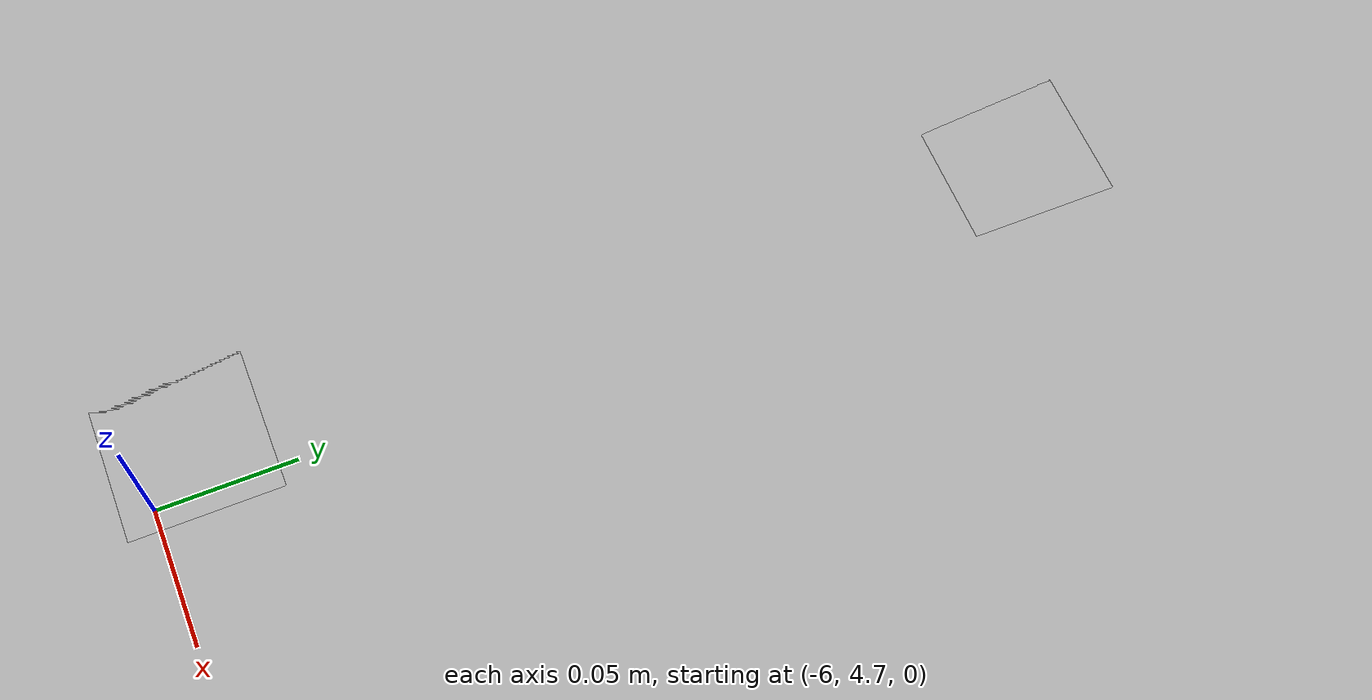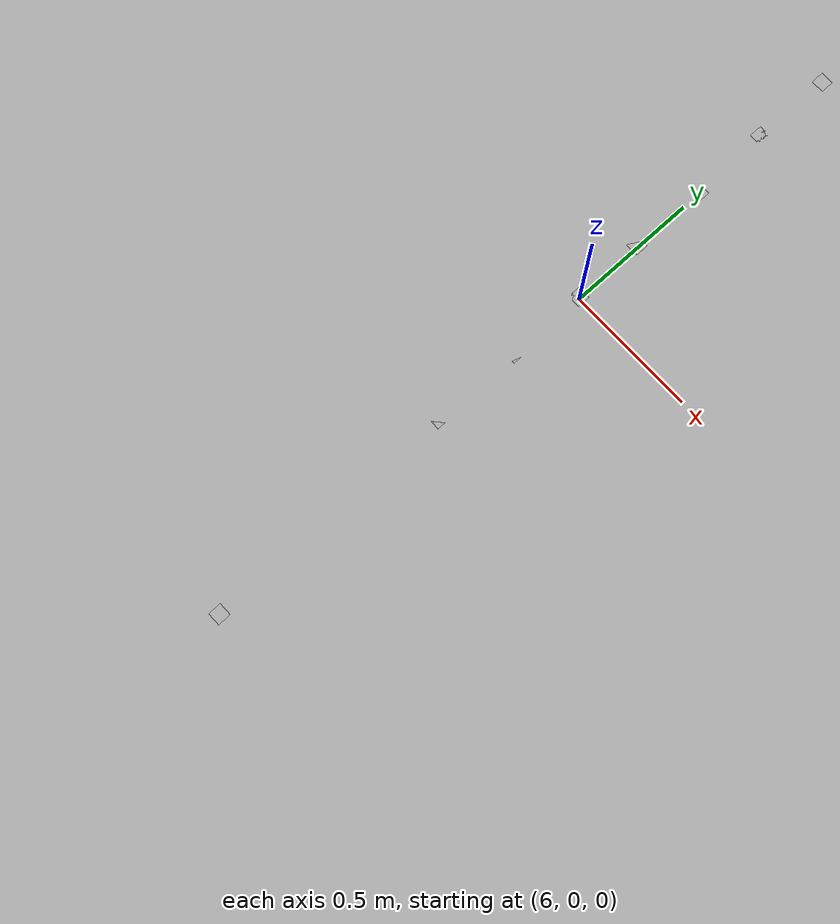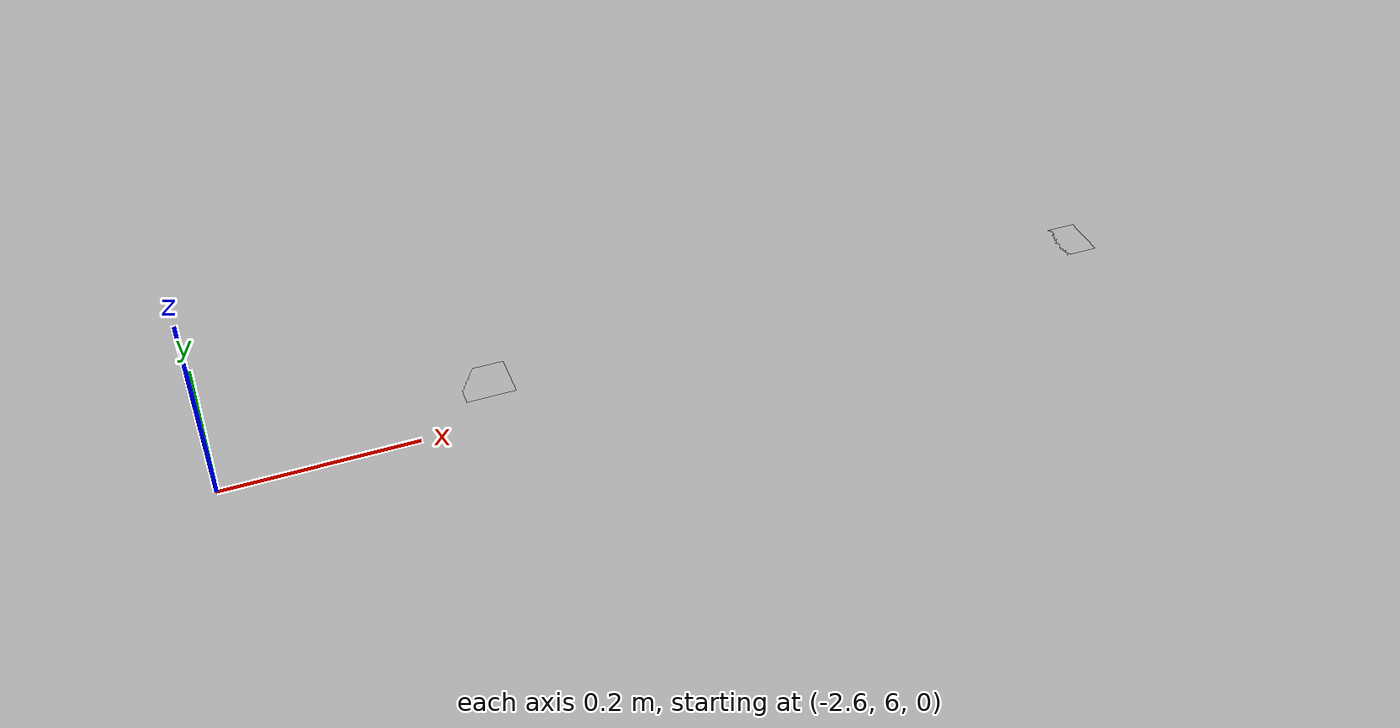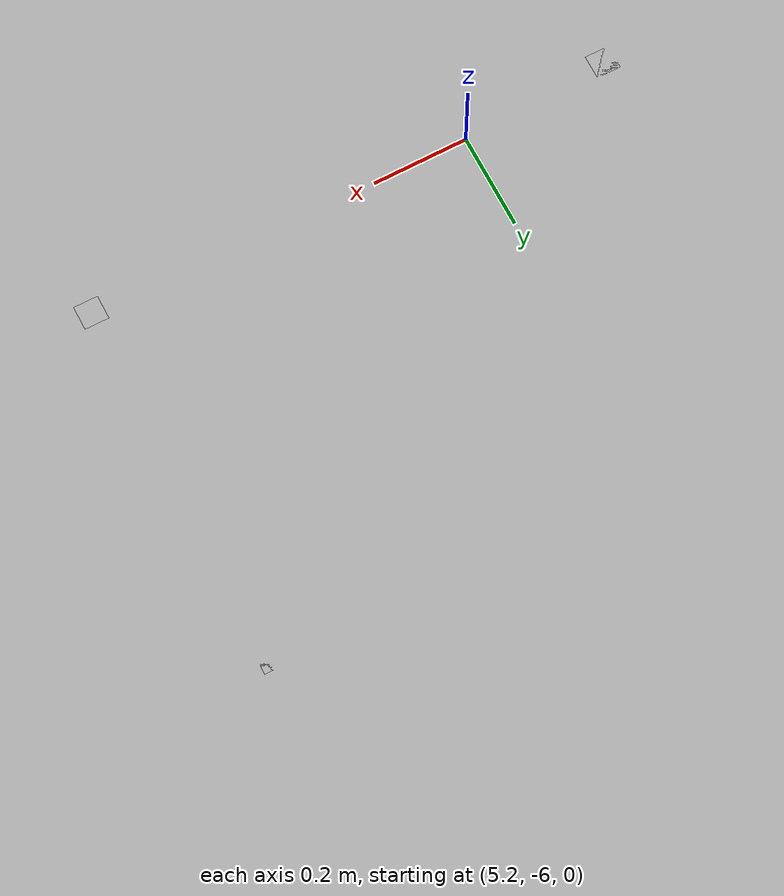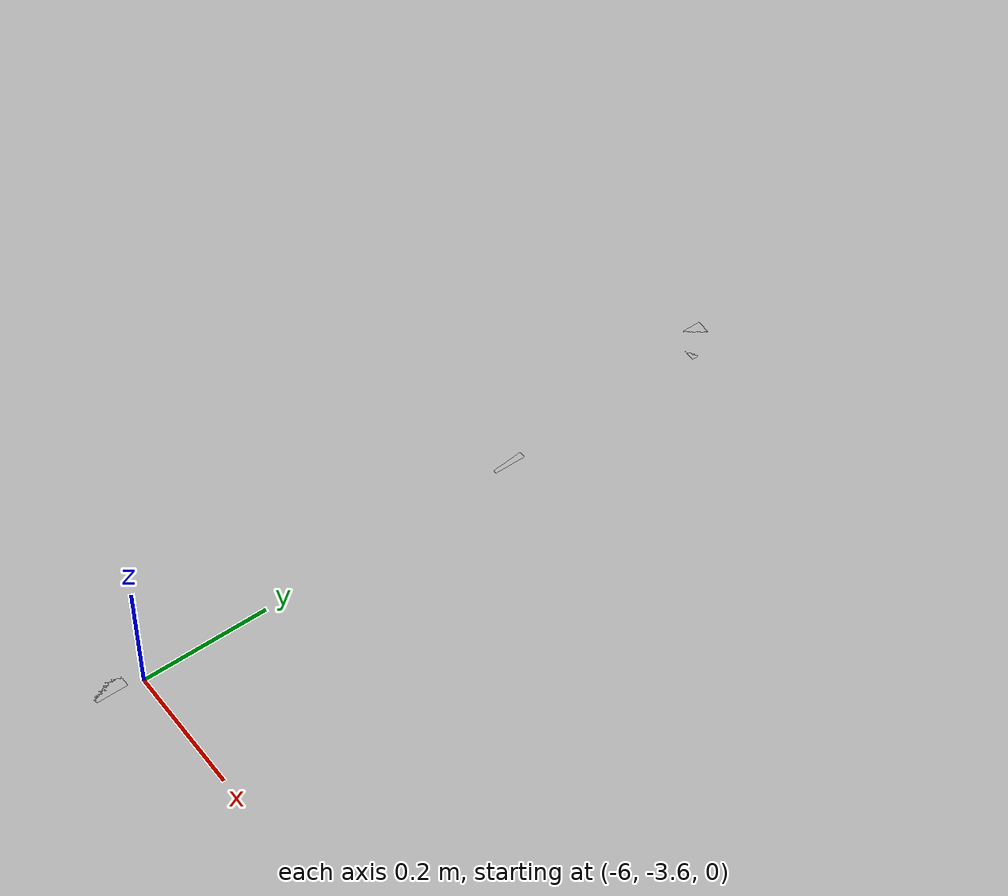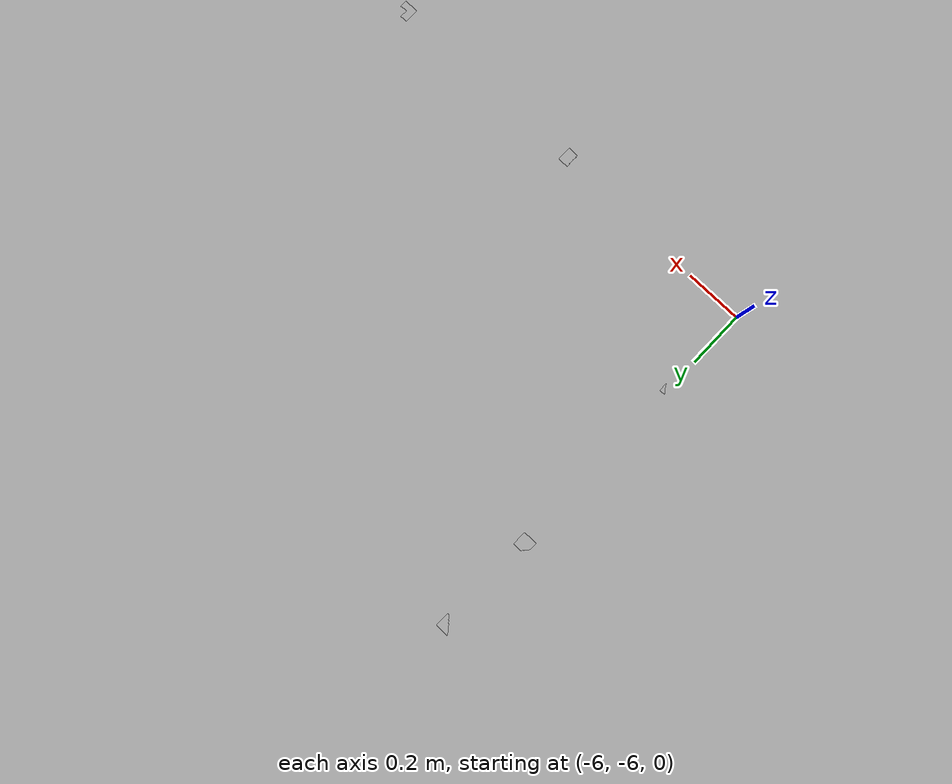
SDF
<sdf version="1.6">
 <world name="default">
  <model name="ground_plane">
   <static>1</static>
   <link name="link">
    <collision name="collision">
     <geometry><plane><normal>0 0 1</normal><size>100 100</size></plane></geometry>
     <surface><friction><ode><mu>100</mu><mu2>50</mu2></ode></friction></surface>
    </collision>
    <visual name="visual">
     <cast_shadows>0</cast_shadows>
     <geometry><plane><normal>0 0 1</normal><size>100 100</size></plane></geometry>
     <material>
      <script><uri>file://media/materials/scripts/gazebo.material</uri><name>Gazebo/Grey</name></script>
     </material>
    </visual>
   </link>
  </model>
  <light name="sun" type="directional">
   <pose>0 0 10 0 -0 0</pose>
   <diffuse>0.8 0.8 0.8 1</diffuse>
   <specular>0.1 0.1 0.1 1</specular>
   <attenuation>
    <range>1000</range>
    <constant>0.9</constant>
    <linear>0.01</linear>
    <quadratic>0.001</quadratic>
   </attenuation>
   <direction>-0.5 0.5 -1</direction>
  </light>
  <plugin name="SetupWorld" filename="libgazebo_plugins.so"/>
  <gravity>0 0 -9.8</gravity>
  <magnetic_field>6e-06 2.3e-05 -4.2e-05</magnetic_field>
  <atmosphere type="adiabatic"/>
  <physics name="default_physics" default="0" type="ode">
   <max_step_size>0.001</max_step_size>
   <real_time_factor>1</real_time_factor>
   <real_time_update_rate>1000</real_time_update_rate>
  </physics>
  <scene><ambient>0.4 0.4 0.4 1</ambient><background>0.7 0.7 0.7 1</background><shadows>1</shadows></scene>
  <spherical_coordinates>
   <surface_model>EARTH_WGS84</surface_model>
   <latitude_deg>0</latitude_deg>
   <longitude_deg>0</longitude_deg>
   <elevation>0</elevation>
   <heading_deg>0</heading_deg>
  </spherical_coordinates>
  <model name="Barrier_West">
   <static>1</static>
   <link name="link">
    <inertial>
     <mass>1</mass>
     <inertia><ixx>0.083</ixx><ixy>0</ixy><ixz>0</ixz><iyy>0</iyy><iyz>0</iyz><izz>0.083</izz></inertia>
    </inertial>
    <collision name="collision">
     <geometry><box><size>0.05 14 0.33</size></box></geometry>
     <surface><friction><ode><mu>1</mu><mu2>1</mu2><slip1>0</slip1><slip2>0</slip2></ode></friction></surface>
    </collision>
    <visual name="visual">
     <geometry><box><size>0.05 14 0.33</size></box></geometry>
     <material>
      <ambient>255 131 0 1</ambient>
      <diffuse>255 131 0 1</diffuse>
      <specular>0.1 0.1 0.1 1</specular>
      <emissive>0 0 0 0</emissive>
     </material>
    </visual>
   </link>
   <pose>-7 0 0 0 -0 0</pose>
  </model>
  <model name="Barrier_North">
   <static>1</static>
   <link name="link">
    <inertial>
     <mass>1</mass>
     <inertia><ixx>0.083</ixx><ixy>0</ixy><ixz>0</ixz><iyy>0</iyy><iyz>0</iyz><izz>0.083</izz></inertia>
    </inertial>
    <collision name="collision">
     <geometry><box><size>0.05 14 0.33</size></box></geometry>
     <surface><friction><ode><mu>1</mu><mu2>1</mu2><slip1>0</slip1><slip2>0</slip2></ode></friction></surface>
    </collision>
    <visual name="visual">
     <geometry><box><size>0.05 14 0.33</size></box></geometry>
     <material>
      <ambient>255 131 0 1</ambient>
      <diffuse>255 131 0 1</diffuse>
      <specular>0.1 0.1 0.1 1</specular>
      <emissive>0 0 0 0</emissive>
     </material>
    </visual>
   </link>
   <pose>0 -7 0 0 -0 1.5708</pose>
  </model>
  <model name="Barrier_East">
   <static>1</static>
   <link name="link">
    <inertial>
     <mass>1</mass>
     <inertia><ixx>0.083</ixx><ixy>0</ixy><ixz>0</ixz><iyy>0</iyy><iyz>0</iyz><izz>0.083</izz></inertia>
    </inertial>
    <collision name="collision">
     <geometry><box><size>0.05 14 0.33</size></box></geometry>
     <surface><friction><ode><mu>1</mu><mu2>1</mu2><slip1>0</slip1><slip2>0</slip2></ode></friction></surface>
    </collision>
    <visual name="visual">
     <geometry><box><size>0.05 14 0.33</size></box></geometry>
     <material>
      <ambient>255 131 0 1</ambient>
      <diffuse>255 131 0 1</diffuse>
      <specular>0.1 0.1 0.1 1</specular>
      <emissive>0 0 0 0</emissive>
     </material>
    </visual>
   </link>
   <pose>7 0 0 0 -0 0</pose>
  </model>
  <model name="Barrier_South">
   <static>1</static>
   <link name="link">
    <inertial>
     <mass>1</mass>
     <inertia><ixx>0.083</ixx><ixy>0</ixy><ixz>0</ixz><iyy>0</iyy><iyz>0</iyz><izz>0.083</izz></inertia>
    </inertial>
    <collision name="collision">
     <geometry><box><size>0.05 14 0.33</size></box></geometry>
     <surface><friction><ode><mu>1</mu><mu2>1</mu2><slip1>0</slip1><slip2>0</slip2></ode></friction></surface>
    </collision>
    <visual name="visual">
     <geometry><box><size>0.05 14 0.33</size></box></geometry>
     <material>
      <ambient>255 131 0 1</ambient>
      <diffuse>255 131 0 1</diffuse>
      <specular>0.1 0.1 0.1 1</specular>
      <emissive>0 0 0 0</emissive>
     </material>
    </visual>
   </link>
   <pose>0 7 0 0 -0 1.5708</pose>
  </model>
  <model name="concrete_ground_plane">
   <static>1</static>
   <link name="link">
    <collision name="collision">
     <geometry><plane><normal>0 0 1</normal><size>100 100</size></plane></geometry>
     <surface><friction><ode><mu>100</mu><mu2>50</mu2></ode></friction></surface>
    </collision>
    <visual name="visual">
     <cast_shadows>0</cast_shadows>
     <geometry><plane><normal>0 0 1</normal><size>100 100</size></plane></geometry>
     <material>
      <script>
       <uri>model://media/materials/scripts</uri>
       <uri>model://media/materials/textures</uri>
       <name>ConcreteGroundPlane/Image</name>
      </script>
     </material>
    </visual>
   </link>
  </model>
  <model name="collection_disk">
   <static>1</static>
   <link name="link">
    <visual name="visual">
     <geometry><box><size>1.016 1.016 0.001</size></box></geometry>
     <material>
      <script>
       <uri>model://collection_disk/materials/scripts</uri>
       <uri>model://collection_disk/materials/textures</uri>
       <name>collection_disk/Diffuse</name>
      </script>
     </material>
    </visual>
   </link>
   <plugin name="score_sim" filename="libgazebo_plugins_score.so">
    <scoreTopic>/collectionZone/score</scoreTopic>
    <collectionZoneSquareSize>1.016</collectionZoneSquareSize>
    <updateRate>0.2</updateRate>
    <robotNamespace>/</robotNamespace>
   </plugin>
  </model>
  <model name="at0">
   <static>0</static>
   <link name="link">
    <inertial>
     <mass>0.01</mass>
     <inertia><ixx>4e-05</ixx><ixy>0</ixy><ixz>0</ixz><iyy>4e-05</iyy><iyz>0</iyz><izz>4e-05</izz></inertia>
    </inertial>
    <visual name="visual">
     <geometry><box><size>0.05 0.05 0.05</size></box></geometry>
     <material>
      <script>
       <uri>model://at0/materials/scripts</uri>
       <uri>model://at0/materials/textures</uri>
       <name>at0/Diffuse</name>
      </script>
     </material>
    </visual>
    <collision name="collision">
     <geometry><box><size>0.05 0.05 0.05</size></box></geometry>
     <surface><friction><ode><mu>0.8</mu><mu2>0.7</mu2></ode></friction></surface>
    </collision>
   </link>
   <pose>-5.98993 6.01178 0.02499 0 2e-06 0</pose>
  </model>
  <model name="at0_0">
   <static>0</static>
   <link name="link">
    <inertial>
     <mass>0.01</mass>
     <inertia><ixx>4e-05</ixx><ixy>0</ixy><ixz>0</ixz><iyy>4e-05</iyy><iyz>0</iyz><izz>4e-05</izz></inertia>
    </inertial>
    <visual name="visual">
     <geometry><box><size>0.05 0.05 0.05</size></box></geometry>
     <material>
      <script>
       <uri>model://at0/materials/scripts</uri>
       <uri>model://at0/materials/textures</uri>
       <name>at0/Diffuse</name>
      </script>
     </material>
    </visual>
    <collision name="collision">
     <geometry><box><size>0.05 0.05 0.05</size></box></geometry>
     <surface><friction><ode><mu>0.8</mu><mu2>0.7</mu2></ode></friction></surface>
    </collision>
   </link>
   <pose>-5.99633 5.00479 0.025 0 -2e-06 0</pose>
  </model>
  <model name="at0_1">
   <static>0</static>
   <link name="link">
    <inertial>
     <mass>0.01</mass>
     <inertia><ixx>4e-05</ixx><ixy>0</ixy><ixz>0</ixz><iyy>4e-05</iyy><iyz>0</iyz><izz>4e-05</izz></inertia>
    </inertial>
    <visual name="visual">
     <geometry><box><size>0.05 0.05 0.05</size></box></geometry>
     <material>
      <script>
       <uri>model://at0/materials/scripts</uri>
       <uri>model://at0/materials/textures</uri>
       <name>at0/Diffuse</name>
      </script>
     </material>
    </visual>
    <collision name="collision">
     <geometry><box><size>0.05 0.05 0.05</size></box></geometry>
     <surface><friction><ode><mu>0.8</mu><mu2>0.7</mu2></ode></friction></surface>
    </collision>
   </link>
   <pose>-6.00836 3.99623 0.02499 0 2e-06 0</pose>
  </model>
  <model name="at0_2">
   <static>0</static>
   <link name="link">
    <inertial>
     <mass>0.01</mass>
     <inertia><ixx>4e-05</ixx><ixy>0</ixy><ixz>0</ixz><iyy>4e-05</iyy><iyz>0</iyz><izz>4e-05</izz></inertia>
    </inertial>
    <visual name="visual">
     <geometry><box><size>0.05 0.05 0.05</size></box></geometry>
     <material>
      <script>
       <uri>model://at0/materials/scripts</uri>
       <uri>model://at0/materials/textures</uri>
       <name>at0/Diffuse</name>
      </script>
     </material>
    </visual>
    <collision name="collision">
     <geometry><box><size>0.05 0.05 0.05</size></box></geometry>
     <surface><friction><ode><mu>0.8</mu><mu2>0.7</mu2></ode></friction></surface>
    </collision>
   </link>
   <pose>-6.00698 3.00028 0.025 0 -2e-06 0</pose>
  </model>
  <model name="at0_7">
   <static>0</static>
   <link name="link">
    <inertial>
     <mass>0.01</mass>
     <inertia><ixx>4e-05</ixx><ixy>0</ixy><ixz>0</ixz><iyy>4e-05</iyy><iyz>0</iyz><izz>4e-05</izz></inertia>
    </inertial>
    <visual name="visual">
     <geometry><box><size>0.05 0.05 0.05</size></box></geometry>
     <material>
      <script>
       <uri>model://at0/materials/scripts</uri>
       <uri>model://at0/materials/textures</uri>
       <name>at0/Diffuse</name>
      </script>
     </material>
    </visual>
    <collision name="collision">
     <geometry><box><size>0.05 0.05 0.05</size></box></geometry>
     <surface><friction><ode><mu>0.8</mu><mu2>0.7</mu2></ode></friction></surface>
    </collision>
   </link>
   <pose>-6.00009 -1.99411 0.02499 0 2e-06 0</pose>
  </model>
  <model name="at0_8">
   <static>0</static>
   <link name="link">
    <inertial>
     <mass>0.01</mass>
     <inertia><ixx>4e-05</ixx><ixy>0</ixy><ixz>0</ixz><iyy>4e-05</iyy><iyz>0</iyz><izz>4e-05</izz></inertia>
    </inertial>
    <visual name="visual">
     <geometry><box><size>0.05 0.05 0.05</size></box></geometry>
     <material>
      <script>
       <uri>model://at0/materials/scripts</uri>
       <uri>model://at0/materials/textures</uri>
       <name>at0/Diffuse</name>
      </script>
     </material>
    </visual>
    <collision name="collision">
     <geometry><box><size>0.05 0.05 0.05</size></box></geometry>
     <surface><friction><ode><mu>0.8</mu><mu2>0.7</mu2></ode></friction></surface>
    </collision>
   </link>
   <pose>-6.00042 -3.00006 0.025 0 -2e-06 0</pose>
  </model>
  <model name="at0_9">
   <static>0</static>
   <link name="link">
    <inertial>
     <mass>0.01</mass>
     <inertia><ixx>4e-05</ixx><ixy>0</ixy><ixz>0</ixz><iyy>4e-05</iyy><iyz>0</iyz><izz>4e-05</izz></inertia>
    </inertial>
    <visual name="visual">
     <geometry><box><size>0.05 0.05 0.05</size></box></geometry>
     <material>
      <script>
       <uri>model://at0/materials/scripts</uri>
       <uri>model://at0/materials/textures</uri>
       <name>at0/Diffuse</name>
      </script>
     </material>
    </visual>
    <collision name="collision">
     <geometry><box><size>0.05 0.05 0.05</size></box></geometry>
     <surface><friction><ode><mu>0.8</mu><mu2>0.7</mu2></ode></friction></surface>
    </collision>
   </link>
   <pose>-5.99748 -3.99837 0.02499 0 2e-06 0</pose>
  </model>
  <model name="at0_10">
   <static>0</static>
   <link name="link">
    <inertial>
     <mass>0.01</mass>
     <inertia><ixx>4e-05</ixx><ixy>0</ixy><ixz>0</ixz><iyy>4e-05</iyy><iyz>0</iyz><izz>4e-05</izz></inertia>
    </inertial>
    <visual name="visual">
     <geometry><box><size>0.05 0.05 0.05</size></box></geometry>
     <material>
      <script>
       <uri>model://at0/materials/scripts</uri>
       <uri>model://at0/materials/textures</uri>
       <name>at0/Diffuse</name>
      </script>
     </material>
    </visual>
    <collision name="collision">
     <geometry><box><size>0.05 0.05 0.05</size></box></geometry>
     <surface><friction><ode><mu>0.8</mu><mu2>0.7</mu2></ode></friction></surface>
    </collision>
   </link>
   <pose>-5.99954 -4.9986 0.025 0 -2e-06 0</pose>
  </model>
  <model name="at0_11">
   <static>0</static>
   <link name="link">
    <inertial>
     <mass>0.01</mass>
     <inertia><ixx>4e-05</ixx><ixy>0</ixy><ixz>0</ixz><iyy>4e-05</iyy><iyz>0</iyz><izz>4e-05</izz></inertia>
    </inertial>
    <visual name="visual">
     <geometry><box><size>0.05 0.05 0.05</size></box></geometry>
     <material>
      <script>
       <uri>model://at0/materials/scripts</uri>
       <uri>model://at0/materials/textures</uri>
       <name>at0/Diffuse</name>
      </script>
     </material>
    </visual>
    <collision name="collision">
     <geometry><box><size>0.05 0.05 0.05</size></box></geometry>
     <surface><friction><ode><mu>0.8</mu><mu2>0.7</mu2></ode></friction></surface>
    </collision>
   </link>
   <pose>-6.002 -6.00125 0.02499 0 2e-06 0</pose>
  </model>
  <model name="at0_12">
   <static>0</static>
   <link name="link">
    <inertial>
     <mass>0.01</mass>
     <inertia><ixx>4e-05</ixx><ixy>0</ixy><ixz>0</ixz><iyy>4e-05</iyy><iyz>0</iyz><izz>4e-05</izz></inertia>
    </inertial>
    <visual name="visual">
     <geometry><box><size>0.05 0.05 0.05</size></box></geometry>
     <material>
      <script>
       <uri>model://at0/materials/scripts</uri>
       <uri>model://at0/materials/textures</uri>
       <name>at0/Diffuse</name>
      </script>
     </material>
    </visual>
    <collision name="collision">
     <geometry><box><size>0.05 0.05 0.05</size></box></geometry>
     <surface><friction><ode><mu>0.8</mu><mu2>0.7</mu2></ode></friction></surface>
    </collision>
   </link>
   <pose>-5.99552 5.67418 0.025 0 -2e-06 0</pose>
  </model>
  <model name="at0_13">
   <static>0</static>
   <link name="link">
    <inertial>
     <mass>0.01</mass>
     <inertia><ixx>4e-05</ixx><ixy>0</ixy><ixz>0</ixz><iyy>4e-05</iyy><iyz>0</iyz><izz>4e-05</izz></inertia>
    </inertial>
    <visual name="visual">
     <geometry><box><size>0.05 0.05 0.05</size></box></geometry>
     <material>
      <script>
       <uri>model://at0/materials/scripts</uri>
       <uri>model://at0/materials/textures</uri>
       <name>at0/Diffuse</name>
      </script>
     </material>
    </visual>
    <collision name="collision">
     <geometry><box><size>0.05 0.05 0.05</size></box></geometry>
     <surface><friction><ode><mu>0.8</mu><mu2>0.7</mu2></ode></friction></surface>
    </collision>
   </link>
   <pose>-5.99881 5.36367 0.02499 0 2e-06 0</pose>
  </model>
  <model name="at0_14">
   <static>0</static>
   <link name="link">
    <inertial>
     <mass>0.01</mass>
     <inertia><ixx>4e-05</ixx><ixy>0</ixy><ixz>0</ixz><iyy>4e-05</iyy><iyz>0</iyz><izz>4e-05</izz></inertia>
    </inertial>
    <visual name="visual">
     <geometry><box><size>0.05 0.05 0.05</size></box></geometry>
     <material>
      <script>
       <uri>model://at0/materials/scripts</uri>
       <uri>model://at0/materials/textures</uri>
       <name>at0/Diffuse</name>
      </script>
     </material>
    </visual>
    <collision name="collision">
     <geometry><box><size>0.05 0.05 0.05</size></box></geometry>
     <surface><friction><ode><mu>0.8</mu><mu2>0.7</mu2></ode></friction></surface>
    </collision>
   </link>
   <pose>-5.9965 4.72016 0.025 0 -2e-06 0</pose>
  </model>
  <model name="at0_15">
   <static>0</static>
   <link name="link">
    <inertial>
     <mass>0.01</mass>
     <inertia><ixx>4e-05</ixx><ixy>0</ixy><ixz>0</ixz><iyy>4e-05</iyy><iyz>0</iyz><izz>4e-05</izz></inertia>
    </inertial>
    <visual name="visual">
     <geometry><box><size>0.05 0.05 0.05</size></box></geometry>
     <material>
      <script>
       <uri>model://at0/materials/scripts</uri>
       <uri>model://at0/materials/textures</uri>
       <name>at0/Diffuse</name>
      </script>
     </material>
    </visual>
    <collision name="collision">
     <geometry><box><size>0.05 0.05 0.05</size></box></geometry>
     <surface><friction><ode><mu>0.8</mu><mu2>0.7</mu2></ode></friction></surface>
    </collision>
   </link>
   <pose>-6.00246 4.35478 0.02499 0 2e-06 0</pose>
  </model>
  <model name="at0_16">
   <static>0</static>
   <link name="link">
    <inertial>
     <mass>0.01</mass>
     <inertia><ixx>4e-05</ixx><ixy>0</ixy><ixz>0</ixz><iyy>4e-05</iyy><iyz>0</iyz><izz>4e-05</izz></inertia>
    </inertial>
    <visual name="visual">
     <geometry><box><size>0.05 0.05 0.05</size></box></geometry>
     <material>
      <script>
       <uri>model://at0/materials/scripts</uri>
       <uri>model://at0/materials/textures</uri>
       <name>at0/Diffuse</name>
      </script>
     </material>
    </visual>
    <collision name="collision">
     <geometry><box><size>0.05 0.05 0.05</size></box></geometry>
     <surface><friction><ode><mu>0.8</mu><mu2>0.7</mu2></ode></friction></surface>
    </collision>
   </link>
   <pose>-5.99948 3.69263 0.02499 0 2e-06 0</pose>
  </model>
  <model name="at0_17">
   <static>0</static>
   <link name="link">
    <inertial>
     <mass>0.01</mass>
     <inertia><ixx>4e-05</ixx><ixy>0</ixy><ixz>0</ixz><iyy>4e-05</iyy><iyz>0</iyz><izz>4e-05</izz></inertia>
    </inertial>
    <visual name="visual">
     <geometry><box><size>0.05 0.05 0.05</size></box></geometry>
     <material>
      <script>
       <uri>model://at0/materials/scripts</uri>
       <uri>model://at0/materials/textures</uri>
       <name>at0/Diffuse</name>
      </script>
     </material>
    </visual>
    <collision name="collision">
     <geometry><box><size>0.05 0.05 0.05</size></box></geometry>
     <surface><friction><ode><mu>0.8</mu><mu2>0.7</mu2></ode></friction></surface>
    </collision>
   </link>
   <pose>-6.00014 3.3548 0.025 0 -2e-06 0</pose>
  </model>
  <model name="at0_18">
   <static>0</static>
   <link name="link">
    <inertial>
     <mass>0.01</mass>
     <inertia><ixx>4e-05</ixx><ixy>0</ixy><ixz>0</ixz><iyy>4e-05</iyy><iyz>0</iyz><izz>4e-05</izz></inertia>
    </inertial>
    <visual name="visual">
     <geometry><box><size>0.05 0.05 0.05</size></box></geometry>
     <material>
      <script>
       <uri>model://at0/materials/scripts</uri>
       <uri>model://at0/materials/textures</uri>
       <name>at0/Diffuse</name>
      </script>
     </material>
    </visual>
    <collision name="collision">
     <geometry><box><size>0.05 0.05 0.05</size></box></geometry>
     <surface><friction><ode><mu>0.8</mu><mu2>0.7</mu2></ode></friction></surface>
    </collision>
   </link>
   <pose>-5.99611 2.72935 0.02499 0 2e-06 0</pose>
  </model>
  <model name="at0_19">
   <static>0</static>
   <link name="link">
    <inertial>
     <mass>0.01</mass>
     <inertia><ixx>4e-05</ixx><ixy>0</ixy><ixz>0</ixz><iyy>4e-05</iyy><iyz>0</iyz><izz>4e-05</izz></inertia>
    </inertial>
    <visual name="visual">
     <geometry><box><size>0.05 0.05 0.05</size></box></geometry>
     <material>
      <script>
       <uri>model://at0/materials/scripts</uri>
       <uri>model://at0/materials/textures</uri>
       <name>at0/Diffuse</name>
      </script>
     </material>
    </visual>
    <collision name="collision">
     <geometry><box><size>0.05 0.05 0.05</size></box></geometry>
     <surface><friction><ode><mu>0.8</mu><mu2>0.7</mu2></ode></friction></surface>
    </collision>
   </link>
   <pose>-6.00066 2.35964 0.025 0 -2e-06 0</pose>
  </model>
  <model name="at0_20">
   <static>0</static>
   <link name="link">
    <inertial>
     <mass>0.01</mass>
     <inertia><ixx>4e-05</ixx><ixy>0</ixy><ixz>0</ixz><iyy>4e-05</iyy><iyz>0</iyz><izz>4e-05</izz></inertia>
    </inertial>
    <visual name="visual">
     <geometry><box><size>0.05 0.05 0.05</size></box></geometry>
     <material>
      <script>
       <uri>model://at0/materials/scripts</uri>
       <uri>model://at0/materials/textures</uri>
       <name>at0/Diffuse</name>
      </script>
     </material>
    </visual>
    <collision name="collision">
     <geometry><box><size>0.05 0.05 0.05</size></box></geometry>
     <surface><friction><ode><mu>0.8</mu><mu2>0.7</mu2></ode></friction></surface>
    </collision>
   </link>
   <pose>-5.99976 1.76991 0.02499 0 2e-06 0</pose>
  </model>
  <model name="at0_21">
   <static>0</static>
   <link name="link">
    <inertial>
     <mass>0.01</mass>
     <inertia><ixx>4e-05</ixx><ixy>0</ixy><ixz>0</ixz><iyy>4e-05</iyy><iyz>0</iyz><izz>4e-05</izz></inertia>
    </inertial>
    <visual name="visual">
     <geometry><box><size>0.05 0.05 0.05</size></box></geometry>
     <material>
      <script>
       <uri>model://at0/materials/scripts</uri>
       <uri>model://at0/materials/textures</uri>
       <name>at0/Diffuse</name>
      </script>
     </material>
    </visual>
    <collision name="collision">
     <geometry><box><size>0.05 0.05 0.05</size></box></geometry>
     <surface><friction><ode><mu>0.8</mu><mu2>0.7</mu2></ode></friction></surface>
    </collision>
   </link>
   <pose>-5.99905 1.36276 0.025 0 -2e-06 0</pose>
  </model>
  <model name="at0_24">
   <static>0</static>
   <link name="link">
    <inertial>
     <mass>0.01</mass>
     <inertia><ixx>4e-05</ixx><ixy>0</ixy><ixz>0</ixz><iyy>4e-05</iyy><iyz>0</iyz><izz>4e-05</izz></inertia>
    </inertial>
    <visual name="visual">
     <geometry><box><size>0.05 0.05 0.05</size></box></geometry>
     <material>
      <script>
       <uri>model://at0/materials/scripts</uri>
       <uri>model://at0/materials/textures</uri>
       <name>at0/Diffuse</name>
      </script>
     </material>
    </visual>
    <collision name="collision">
     <geometry><box><size>0.05 0.05 0.05</size></box></geometry>
     <surface><friction><ode><mu>0.8</mu><mu2>0.7</mu2></ode></friction></surface>
    </collision>
   </link>
   <pose>-5.99908 -2.28188 0.02499 0 2e-06 0</pose>
  </model>
  <model name="at0_25">
   <static>0</static>
   <link name="link">
    <inertial>
     <mass>0.01</mass>
     <inertia><ixx>4e-05</ixx><ixy>0</ixy><ixz>0</ixz><iyy>4e-05</iyy><iyz>0</iyz><izz>4e-05</izz></inertia>
    </inertial>
    <visual name="visual">
     <geometry><box><size>0.05 0.05 0.05</size></box></geometry>
     <material>
      <script>
       <uri>model://at0/materials/scripts</uri>
       <uri>model://at0/materials/textures</uri>
       <name>at0/Diffuse</name>
      </script>
     </material>
    </visual>
    <collision name="collision">
     <geometry><box><size>0.05 0.05 0.05</size></box></geometry>
     <surface><friction><ode><mu>0.8</mu><mu2>0.7</mu2></ode></friction></surface>
    </collision>
   </link>
   <pose>-6.00138 -2.64982 0.025 0 -2e-06 0</pose>
  </model>
  <model name="at0_26">
   <static>0</static>
   <link name="link">
    <inertial>
     <mass>0.01</mass>
     <inertia><ixx>4e-05</ixx><ixy>0</ixy><ixz>0</ixz><iyy>4e-05</iyy><iyz>0</iyz><izz>4e-05</izz></inertia>
    </inertial>
    <visual name="visual">
     <geometry><box><size>0.05 0.05 0.05</size></box></geometry>
     <material>
      <script>
       <uri>model://at0/materials/scripts</uri>
       <uri>model://at0/materials/textures</uri>
       <name>at0/Diffuse</name>
      </script>
     </material>
    </visual>
    <collision name="collision">
     <geometry><box><size>0.05 0.05 0.05</size></box></geometry>
     <surface><friction><ode><mu>0.8</mu><mu2>0.7</mu2></ode></friction></surface>
    </collision>
   </link>
   <pose>-5.99997 -3.34464 0.02499 0 2e-06 0</pose>
  </model>
  <model name="at0_27">
   <static>0</static>
   <link name="link">
    <inertial>
     <mass>0.01</mass>
     <inertia><ixx>4e-05</ixx><ixy>0</ixy><ixz>0</ixz><iyy>4e-05</iyy><iyz>0</iyz><izz>4e-05</izz></inertia>
    </inertial>
    <visual name="visual">
     <geometry><box><size>0.05 0.05 0.05</size></box></geometry>
     <material>
      <script>
       <uri>model://at0/materials/scripts</uri>
       <uri>model://at0/materials/textures</uri>
       <name>at0/Diffuse</name>
      </script>
     </material>
    </visual>
    <collision name="collision">
     <geometry><box><size>0.05 0.05 0.05</size></box></geometry>
     <surface><friction><ode><mu>0.8</mu><mu2>0.7</mu2></ode></friction></surface>
    </collision>
   </link>
   <pose>-6.00019 -3.6617 0.025 0 -2e-06 0</pose>
  </model>
  <model name="at0_28">
   <static>0</static>
   <link name="link">
    <inertial>
     <mass>0.01</mass>
     <inertia><ixx>4e-05</ixx><ixy>0</ixy><ixz>0</ixz><iyy>4e-05</iyy><iyz>0</iyz><izz>4e-05</izz></inertia>
    </inertial>
    <visual name="visual">
     <geometry><box><size>0.05 0.05 0.05</size></box></geometry>
     <material>
      <script>
       <uri>model://at0/materials/scripts</uri>
       <uri>model://at0/materials/textures</uri>
       <name>at0/Diffuse</name>
      </script>
     </material>
    </visual>
    <collision name="collision">
     <geometry><box><size>0.05 0.05 0.05</size></box></geometry>
     <surface><friction><ode><mu>0.8</mu><mu2>0.7</mu2></ode></friction></surface>
    </collision>
   </link>
   <pose>-6.00219 -4.27812 0.02499 0 2e-06 0</pose>
  </model>
  <model name="at0_29">
   <static>0</static>
   <link name="link">
    <inertial>
     <mass>0.01</mass>
     <inertia><ixx>4e-05</ixx><ixy>0</ixy><ixz>0</ixz><iyy>4e-05</iyy><iyz>0</iyz><izz>4e-05</izz></inertia>
    </inertial>
    <visual name="visual">
     <geometry><box><size>0.05 0.05 0.05</size></box></geometry>
     <material>
      <script>
       <uri>model://at0/materials/scripts</uri>
       <uri>model://at0/materials/textures</uri>
       <name>at0/Diffuse</name>
      </script>
     </material>
    </visual>
    <collision name="collision">
     <geometry><box><size>0.05 0.05 0.05</size></box></geometry>
     <surface><friction><ode><mu>0.8</mu><mu2>0.7</mu2></ode></friction></surface>
    </collision>
   </link>
   <pose>-5.99889 -4.65315 0.025 0 -2e-06 0</pose>
  </model>
  <model name="at0_30">
   <static>0</static>
   <link name="link">
    <inertial>
     <mass>0.01</mass>
     <inertia><ixx>4e-05</ixx><ixy>0</ixy><ixz>0</ixz><iyy>4e-05</iyy><iyz>0</iyz><izz>4e-05</izz></inertia>
    </inertial>
    <visual name="visual">
     <geometry><box><size>0.05 0.05 0.05</size></box></geometry>
     <material>
      <script>
       <uri>model://at0/materials/scripts</uri>
       <uri>model://at0/materials/textures</uri>
       <name>at0/Diffuse</name>
      </script>
     </material>
    </visual>
    <collision name="collision">
     <geometry><box><size>0.05 0.05 0.05</size></box></geometry>
     <surface><friction><ode><mu>0.8</mu><mu2>0.7</mu2></ode></friction></surface>
    </collision>
   </link>
   <pose>-6.00384 -5.3475 0.02499 0 2e-06 0</pose>
  </model>
  <model name="at0_31">
   <static>0</static>
   <link name="link">
    <inertial>
     <mass>0.01</mass>
     <inertia><ixx>4e-05</ixx><ixy>0</ixy><ixz>0</ixz><iyy>4e-05</iyy><iyz>0</iyz><izz>4e-05</izz></inertia>
    </inertial>
    <visual name="visual">
     <geometry><box><size>0.05 0.05 0.05</size></box></geometry>
     <material>
      <script>
       <uri>model://at0/materials/scripts</uri>
       <uri>model://at0/materials/textures</uri>
       <name>at0/Diffuse</name>
      </script>
     </material>
    </visual>
    <collision name="collision">
     <geometry><box><size>0.05 0.05 0.05</size></box></geometry>
     <surface><friction><ode><mu>0.8</mu><mu2>0.7</mu2></ode></friction></surface>
    </collision>
   </link>
   <pose>-6.00194 -5.66903 0.025 0 -2e-06 0</pose>
  </model>
  <model name="at0_35">
   <static>0</static>
   <link name="link">
    <inertial>
     <mass>0.01</mass>
     <inertia><ixx>4e-05</ixx><ixy>0</ixy><ixz>0</ixz><iyy>4e-05</iyy><iyz>0</iyz><izz>4e-05</izz></inertia>
    </inertial>
    <visual name="visual">
     <geometry><box><size>0.05 0.05 0.05</size></box></geometry>
     <material>
      <script>
       <uri>model://at0/materials/scripts</uri>
       <uri>model://at0/materials/textures</uri>
       <name>at0/Diffuse</name>
      </script>
     </material>
    </visual>
    <collision name="collision">
     <geometry><box><size>0.05 0.05 0.05</size></box></geometry>
     <surface><friction><ode><mu>0.8</mu><mu2>0.7</mu2></ode></friction></surface>
    </collision>
   </link>
   <pose>-0.998783 6.00048 0.025 0 -2e-06 0</pose>
  </model>
  <model name="at0_36">
   <static>0</static>
   <link name="link">
    <inertial>
     <mass>0.01</mass>
     <inertia><ixx>4e-05</ixx><ixy>0</ixy><ixz>0</ixz><iyy>4e-05</iyy><iyz>0</iyz><izz>4e-05</izz></inertia>
    </inertial>
    <visual name="visual">
     <geometry><box><size>0.05 0.05 0.05</size></box></geometry>
     <material>
      <script>
       <uri>model://at0/materials/scripts</uri>
       <uri>model://at0/materials/textures</uri>
       <name>at0/Diffuse</name>
      </script>
     </material>
    </visual>
    <collision name="collision">
     <geometry><box><size>0.05 0.05 0.05</size></box></geometry>
     <surface><friction><ode><mu>0.8</mu><mu2>0.7</mu2></ode></friction></surface>
    </collision>
   </link>
   <pose>-1.33872 6.00015 0.02499 0 2e-06 0</pose>
  </model>
  <model name="at0_37">
   <static>0</static>
   <link name="link">
    <inertial>
     <mass>0.01</mass>
     <inertia><ixx>4e-05</ixx><ixy>0</ixy><ixz>0</ixz><iyy>4e-05</iyy><iyz>0</iyz><izz>4e-05</izz></inertia>
    </inertial>
    <visual name="visual">
     <geometry><box><size>0.05 0.05 0.05</size></box></geometry>
     <material>
      <script>
       <uri>model://at0/materials/scripts</uri>
       <uri>model://at0/materials/textures</uri>
       <name>at0/Diffuse</name>
      </script>
     </material>
    </visual>
    <collision name="collision">
     <geometry><box><size>0.05 0.05 0.05</size></box></geometry>
     <surface><friction><ode><mu>0.8</mu><mu2>0.7</mu2></ode></friction></surface>
    </collision>
   </link>
   <pose>-1.67352 6.00471 0.025 0 -2e-06 0</pose>
  </model>
  <model name="at0_38">
   <static>0</static>
   <link name="link">
    <inertial>
     <mass>0.01</mass>
     <inertia><ixx>4e-05</ixx><ixy>0</ixy><ixz>0</ixz><iyy>4e-05</iyy><iyz>0</iyz><izz>4e-05</izz></inertia>
    </inertial>
    <visual name="visual">
     <geometry><box><size>0.05 0.05 0.05</size></box></geometry>
     <material>
      <script>
       <uri>model://at0/materials/scripts</uri>
       <uri>model://at0/materials/textures</uri>
       <name>at0/Diffuse</name>
      </script>
     </material>
    </visual>
    <collision name="collision">
     <geometry><box><size>0.05 0.05 0.05</size></box></geometry>
     <surface><friction><ode><mu>0.8</mu><mu2>0.7</mu2></ode></friction></surface>
    </collision>
   </link>
   <pose>-2.00174 6.00251 0.02499 0 2e-06 0</pose>
  </model>
  <model name="at0_39">
   <static>0</static>
   <link name="link">
    <inertial>
     <mass>0.01</mass>
     <inertia><ixx>4e-05</ixx><ixy>0</ixy><ixz>0</ixz><iyy>4e-05</iyy><iyz>0</iyz><izz>4e-05</izz></inertia>
    </inertial>
    <visual name="visual">
     <geometry><box><size>0.05 0.05 0.05</size></box></geometry>
     <material>
      <script>
       <uri>model://at0/materials/scripts</uri>
       <uri>model://at0/materials/textures</uri>
       <name>at0/Diffuse</name>
      </script>
     </material>
    </visual>
    <collision name="collision">
     <geometry><box><size>0.05 0.05 0.05</size></box></geometry>
     <surface><friction><ode><mu>0.8</mu><mu2>0.7</mu2></ode></friction></surface>
    </collision>
   </link>
   <pose>-2.9927 6.00134 0.025 0 -2e-06 0</pose>
  </model>
  <model name="at0_40">
   <static>0</static>
   <link name="link">
    <inertial>
     <mass>0.01</mass>
     <inertia><ixx>4e-05</ixx><ixy>0</ixy><ixz>0</ixz><iyy>4e-05</iyy><iyz>0</iyz><izz>4e-05</izz></inertia>
    </inertial>
    <visual name="visual">
     <geometry><box><size>0.05 0.05 0.05</size></box></geometry>
     <material>
      <script>
       <uri>model://at0/materials/scripts</uri>
       <uri>model://at0/materials/textures</uri>
       <name>at0/Diffuse</name>
      </script>
     </material>
    </visual>
    <collision name="collision">
     <geometry><box><size>0.05 0.05 0.05</size></box></geometry>
     <surface><friction><ode><mu>0.8</mu><mu2>0.7</mu2></ode></friction></surface>
    </collision>
   </link>
   <pose>-2.67121 6.00366 0.02499 0 2e-06 0</pose>
  </model>
  <model name="at0_41">
   <static>0</static>
   <link name="link">
    <inertial>
     <mass>0.01</mass>
     <inertia><ixx>4e-05</ixx><ixy>0</ixy><ixz>0</ixz><iyy>4e-05</iyy><iyz>0</iyz><izz>4e-05</izz></inertia>
    </inertial>
    <visual name="visual">
     <geometry><box><size>0.05 0.05 0.05</size></box></geometry>
     <material>
      <script>
       <uri>model://at0/materials/scripts</uri>
       <uri>model://at0/materials/textures</uri>
       <name>at0/Diffuse</name>
      </script>
     </material>
    </visual>
    <collision name="collision">
     <geometry><box><size>0.05 0.05 0.05</size></box></geometry>
     <surface><friction><ode><mu>0.8</mu><mu2>0.7</mu2></ode></friction></surface>
    </collision>
   </link>
   <pose>-2.32807 6.00558 0.025 0 -2e-06 0</pose>
  </model>
  <model name="at0_42">
   <static>0</static>
   <link name="link">
    <inertial>
     <mass>0.01</mass>
     <inertia><ixx>4e-05</ixx><ixy>0</ixy><ixz>0</ixz><iyy>4e-05</iyy><iyz>0</iyz><izz>4e-05</izz></inertia>
    </inertial>
    <visual name="visual">
     <geometry><box><size>0.05 0.05 0.05</size></box></geometry>
     <material>
      <script>
       <uri>model://at0/materials/scripts</uri>
       <uri>model://at0/materials/textures</uri>
       <name>at0/Diffuse</name>
      </script>
     </material>
    </visual>
    <collision name="collision">
     <geometry><box><size>0.05 0.05 0.05</size></box></geometry>
     <surface><friction><ode><mu>0.8</mu><mu2>0.7</mu2></ode></friction></surface>
    </collision>
   </link>
   <pose>-3.99349 5.99892 0.02499 0 2e-06 0</pose>
  </model>
  <model name="at0_43">
   <static>0</static>
   <link name="link">
    <inertial>
     <mass>0.01</mass>
     <inertia><ixx>4e-05</ixx><ixy>0</ixy><ixz>0</ixz><iyy>4e-05</iyy><iyz>0</iyz><izz>4e-05</izz></inertia>
    </inertial>
    <visual name="visual">
     <geometry><box><size>0.05 0.05 0.05</size></box></geometry>
     <material>
      <script>
       <uri>model://at0/materials/scripts</uri>
       <uri>model://at0/materials/textures</uri>
       <name>at0/Diffuse</name>
      </script>
     </material>
    </visual>
    <collision name="collision">
     <geometry><box><size>0.05 0.05 0.05</size></box></geometry>
     <surface><friction><ode><mu>0.8</mu><mu2>0.7</mu2></ode></friction></surface>
    </collision>
   </link>
   <pose>-3.63234 6.00216 0.025 0 -2e-06 0</pose>
  </model>
  <model name="at0_44">
   <static>0</static>
   <link name="link">
    <inertial>
     <mass>0.01</mass>
     <inertia><ixx>4e-05</ixx><ixy>0</ixy><ixz>0</ixz><iyy>4e-05</iyy><iyz>0</iyz><izz>4e-05</izz></inertia>
    </inertial>
    <visual name="visual">
     <geometry><box><size>0.05 0.05 0.05</size></box></geometry>
     <material>
      <script>
       <uri>model://at0/materials/scripts</uri>
       <uri>model://at0/materials/textures</uri>
       <name>at0/Diffuse</name>
      </script>
     </material>
    </visual>
    <collision name="collision">
     <geometry><box><size>0.05 0.05 0.05</size></box></geometry>
     <surface><friction><ode><mu>0.8</mu><mu2>0.7</mu2></ode></friction></surface>
    </collision>
   </link>
   <pose>-3.30924 6.0028 0.02499 0 2e-06 0</pose>
  </model>
  <model name="at0_45">
   <static>0</static>
   <link name="link">
    <inertial>
     <mass>0.01</mass>
     <inertia><ixx>4e-05</ixx><ixy>0</ixy><ixz>0</ixz><iyy>4e-05</iyy><iyz>0</iyz><izz>4e-05</izz></inertia>
    </inertial>
    <visual name="visual">
     <geometry><box><size>0.05 0.05 0.05</size></box></geometry>
     <material>
      <script>
       <uri>model://at0/materials/scripts</uri>
       <uri>model://at0/materials/textures</uri>
       <name>at0/Diffuse</name>
      </script>
     </material>
    </visual>
    <collision name="collision">
     <geometry><box><size>0.05 0.05 0.05</size></box></geometry>
     <surface><friction><ode><mu>0.8</mu><mu2>0.7</mu2></ode></friction></surface>
    </collision>
   </link>
   <pose>-4.99838 6.00697 0.025 0 -2e-06 0</pose>
  </model>
  <model name="at0_46">
   <static>0</static>
   <link name="link">
    <inertial>
     <mass>0.01</mass>
     <inertia><ixx>4e-05</ixx><ixy>0</ixy><ixz>0</ixz><iyy>4e-05</iyy><iyz>0</iyz><izz>4e-05</izz></inertia>
    </inertial>
    <visual name="visual">
     <geometry><box><size>0.05 0.05 0.05</size></box></geometry>
     <material>
      <script>
       <uri>model://at0/materials/scripts</uri>
       <uri>model://at0/materials/textures</uri>
       <name>at0/Diffuse</name>
      </script>
     </material>
    </visual>
    <collision name="collision">
     <geometry><box><size>0.05 0.05 0.05</size></box></geometry>
     <surface><friction><ode><mu>0.8</mu><mu2>0.7</mu2></ode></friction></surface>
    </collision>
   </link>
   <pose>-4.616 5.99986 0.02499 0 2e-06 0</pose>
  </model>
  <model name="at0_47">
   <static>0</static>
   <link name="link">
    <inertial>
     <mass>0.01</mass>
     <inertia><ixx>4e-05</ixx><ixy>0</ixy><ixz>0</ixz><iyy>4e-05</iyy><iyz>0</iyz><izz>4e-05</izz></inertia>
    </inertial>
    <visual name="visual">
     <geometry><box><size>0.05 0.05 0.05</size></box></geometry>
     <material>
      <script>
       <uri>model://at0/materials/scripts</uri>
       <uri>model://at0/materials/textures</uri>
       <name>at0/Diffuse</name>
      </script>
     </material>
    </visual>
    <collision name="collision">
     <geometry><box><size>0.05 0.05 0.05</size></box></geometry>
     <surface><friction><ode><mu>0.8</mu><mu2>0.7</mu2></ode></friction></surface>
    </collision>
   </link>
   <pose>-4.26979 6.00172 0.025 0 -2e-06 0</pose>
  </model>
  <model name="at0_48">
   <static>0</static>
   <link name="link">
    <inertial>
     <mass>0.01</mass>
     <inertia><ixx>4e-05</ixx><ixy>0</ixy><ixz>0</ixz><iyy>4e-05</iyy><iyz>0</iyz><izz>4e-05</izz></inertia>
    </inertial>
    <visual name="visual">
     <geometry><box><size>0.05 0.05 0.05</size></box></geometry>
     <material>
      <script>
       <uri>model://at0/materials/scripts</uri>
       <uri>model://at0/materials/textures</uri>
       <name>at0/Diffuse</name>
      </script>
     </material>
    </visual>
    <collision name="collision">
     <geometry><box><size>0.05 0.05 0.05</size></box></geometry>
     <surface><friction><ode><mu>0.8</mu><mu2>0.7</mu2></ode></friction></surface>
    </collision>
   </link>
   <pose>-5.67036 5.9953 0.02499 0 2e-06 0</pose>
  </model>
  <model name="at0_49">
   <static>0</static>
   <link name="link">
    <inertial>
     <mass>0.01</mass>
     <inertia><ixx>4e-05</ixx><ixy>0</ixy><ixz>0</ixz><iyy>4e-05</iyy><iyz>0</iyz><izz>4e-05</izz></inertia>
    </inertial>
    <visual name="visual">
     <geometry><box><size>0.05 0.05 0.05</size></box></geometry>
     <material>
      <script>
       <uri>model://at0/materials/scripts</uri>
       <uri>model://at0/materials/textures</uri>
       <name>at0/Diffuse</name>
      </script>
     </material>
    </visual>
    <collision name="collision">
     <geometry><box><size>0.05 0.05 0.05</size></box></geometry>
     <surface><friction><ode><mu>0.8</mu><mu2>0.7</mu2></ode></friction></surface>
    </collision>
   </link>
   <pose>-5.33252 5.99899 0.025 0 -2e-06 0</pose>
  </model>
  <model name="at0_50">
   <static>0</static>
   <link name="link">
    <inertial>
     <mass>0.01</mass>
     <inertia><ixx>4e-05</ixx><ixy>0</ixy><ixz>0</ixz><iyy>4e-05</iyy><iyz>0</iyz><izz>4e-05</izz></inertia>
    </inertial>
    <visual name="visual">
     <geometry><box><size>0.05 0.05 0.05</size></box></geometry>
     <material>
      <script>
       <uri>model://at0/materials/scripts</uri>
       <uri>model://at0/materials/textures</uri>
       <name>at0/Diffuse</name>
      </script>
     </material>
    </visual>
    <collision name="collision">
     <geometry><box><size>0.05 0.05 0.05</size></box></geometry>
     <surface><friction><ode><mu>0.8</mu><mu2>0.7</mu2></ode></friction></surface>
    </collision>
   </link>
   <pose>1.00427 5.99629 0.02499 0 2e-06 0</pose>
  </model>
  <model name="at0_51">
   <static>0</static>
   <link name="link">
    <inertial>
     <mass>0.01</mass>
     <inertia><ixx>4e-05</ixx><ixy>0</ixy><ixz>0</ixz><iyy>4e-05</iyy><iyz>0</iyz><izz>4e-05</izz></inertia>
    </inertial>
    <visual name="visual">
     <geometry><box><size>0.05 0.05 0.05</size></box></geometry>
     <material>
      <script>
       <uri>model://at0/materials/scripts</uri>
       <uri>model://at0/materials/textures</uri>
       <name>at0/Diffuse</name>
      </script>
     </material>
    </visual>
    <collision name="collision">
     <geometry><box><size>0.05 0.05 0.05</size></box></geometry>
     <surface><friction><ode><mu>0.8</mu><mu2>0.7</mu2></ode></friction></surface>
    </collision>
   </link>
   <pose>6.01358 5.99537 0.025 0 -2e-06 0</pose>
  </model>
  <model name="at0_52">
   <static>0</static>
   <link name="link">
    <inertial>
     <mass>0.01</mass>
     <inertia><ixx>4e-05</ixx><ixy>0</ixy><ixz>0</ixz><iyy>4e-05</iyy><iyz>0</iyz><izz>4e-05</izz></inertia>
    </inertial>
    <visual name="visual">
     <geometry><box><size>0.05 0.05 0.05</size></box></geometry>
     <material>
      <script>
       <uri>model://at0/materials/scripts</uri>
       <uri>model://at0/materials/textures</uri>
       <name>at0/Diffuse</name>
      </script>
     </material>
    </visual>
    <collision name="collision">
     <geometry><box><size>0.05 0.05 0.05</size></box></geometry>
     <surface><friction><ode><mu>0.8</mu><mu2>0.7</mu2></ode></friction></surface>
    </collision>
   </link>
   <pose>5.68648 6.00388 0.02499 0 2e-06 0</pose>
  </model>
  <model name="at0_53">
   <static>0</static>
   <link name="link">
    <inertial>
     <mass>0.01</mass>
     <inertia><ixx>4e-05</ixx><ixy>0</ixy><ixz>0</ixz><iyy>4e-05</iyy><iyz>0</iyz><izz>4e-05</izz></inertia>
    </inertial>
    <visual name="visual">
     <geometry><box><size>0.05 0.05 0.05</size></box></geometry>
     <material>
      <script>
       <uri>model://at0/materials/scripts</uri>
       <uri>model://at0/materials/textures</uri>
       <name>at0/Diffuse</name>
      </script>
     </material>
    </visual>
    <collision name="collision">
     <geometry><box><size>0.05 0.05 0.05</size></box></geometry>
     <surface><friction><ode><mu>0.8</mu><mu2>0.7</mu2></ode></friction></surface>
    </collision>
   </link>
   <pose>5.31001 6.00729 0.02499 0 2e-06 0</pose>
  </model>
  <model name="at0_54">
   <static>0</static>
   <link name="link">
    <inertial>
     <mass>0.01</mass>
     <inertia><ixx>4e-05</ixx><ixy>0</ixy><ixz>0</ixz><iyy>4e-05</iyy><iyz>0</iyz><izz>4e-05</izz></inertia>
    </inertial>
    <visual name="visual">
     <geometry><box><size>0.05 0.05 0.05</size></box></geometry>
     <material>
      <script>
       <uri>model://at0/materials/scripts</uri>
       <uri>model://at0/materials/textures</uri>
       <name>at0/Diffuse</name>
      </script>
     </material>
    </visual>
    <collision name="collision">
     <geometry><box><size>0.05 0.05 0.05</size></box></geometry>
     <surface><friction><ode><mu>0.8</mu><mu2>0.7</mu2></ode></friction></surface>
    </collision>
   </link>
   <pose>4.99395 6.00957 0.02499 0 2e-06 0</pose>
  </model>
  <model name="at0_60">
   <static>0</static>
   <link name="link">
    <inertial>
     <mass>0.01</mass>
     <inertia><ixx>4e-05</ixx><ixy>0</ixy><ixz>0</ixz><iyy>4e-05</iyy><iyz>0</iyz><izz>4e-05</izz></inertia>
    </inertial>
    <visual name="visual">
     <geometry><box><size>0.05 0.05 0.05</size></box></geometry>
     <material>
      <script>
       <uri>model://at0/materials/scripts</uri>
       <uri>model://at0/materials/textures</uri>
       <name>at0/Diffuse</name>
      </script>
     </material>
    </visual>
    <collision name="collision">
     <geometry><box><size>0.05 0.05 0.05</size></box></geometry>
     <surface><friction><ode><mu>0.8</mu><mu2>0.7</mu2></ode></friction></surface>
    </collision>
   </link>
   <pose>6.00456 -1.99199 0.02499 0 2e-06 0</pose>
  </model>
  <model name="at0_61">
   <static>0</static>
   <link name="link">
    <inertial>
     <mass>0.01</mass>
     <inertia><ixx>4e-05</ixx><ixy>0</ixy><ixz>0</ixz><iyy>4e-05</iyy><iyz>0</iyz><izz>4e-05</izz></inertia>
    </inertial>
    <visual name="visual">
     <geometry><box><size>0.05 0.05 0.05</size></box></geometry>
     <material>
      <script>
       <uri>model://at0/materials/scripts</uri>
       <uri>model://at0/materials/textures</uri>
       <name>at0/Diffuse</name>
      </script>
     </material>
    </visual>
    <collision name="collision">
     <geometry><box><size>0.05 0.05 0.05</size></box></geometry>
     <surface><friction><ode><mu>0.8</mu><mu2>0.7</mu2></ode></friction></surface>
    </collision>
   </link>
   <pose>6.00273 -0.011351 0.025 0 -2e-06 0</pose>
  </model>
  <model name="at0_62">
   <static>0</static>
   <link name="link">
    <inertial>
     <mass>0.01</mass>
     <inertia><ixx>4e-05</ixx><ixy>0</ixy><ixz>0</ixz><iyy>4e-05</iyy><iyz>0</iyz><izz>4e-05</izz></inertia>
    </inertial>
    <visual name="visual">
     <geometry><box><size>0.05 0.05 0.05</size></box></geometry>
     <material>
      <script>
       <uri>model://at0/materials/scripts</uri>
       <uri>model://at0/materials/textures</uri>
       <name>at0/Diffuse</name>
      </script>
     </material>
    </visual>
    <collision name="collision">
     <geometry><box><size>0.05 0.05 0.05</size></box></geometry>
     <surface><friction><ode><mu>0.8</mu><mu2>0.7</mu2></ode></friction></surface>
    </collision>
   </link>
   <pose>-6.00899 -0.000138 0.02499 0 2e-06 0</pose>
  </model>
  <model name="at0_63">
   <static>0</static>
   <link name="link">
    <inertial>
     <mass>0.01</mass>
     <inertia><ixx>4e-05</ixx><ixy>0</ixy><ixz>0</ixz><iyy>4e-05</iyy><iyz>0</iyz><izz>4e-05</izz></inertia>
    </inertial>
    <visual name="visual">
     <geometry><box><size>0.05 0.05 0.05</size></box></geometry>
     <material>
      <script>
       <uri>model://at0/materials/scripts</uri>
       <uri>model://at0/materials/textures</uri>
       <name>at0/Diffuse</name>
      </script>
     </material>
    </visual>
    <collision name="collision">
     <geometry><box><size>0.05 0.05 0.05</size></box></geometry>
     <surface><friction><ode><mu>0.8</mu><mu2>0.7</mu2></ode></friction></surface>
    </collision>
   </link>
   <pose>-5.9938 0.402658 0.025 0 -2e-06 0</pose>
  </model>
  <model name="at0_64">
   <static>0</static>
   <link name="link">
    <inertial>
     <mass>0.01</mass>
     <inertia><ixx>4e-05</ixx><ixy>0</ixy><ixz>0</ixz><iyy>4e-05</iyy><iyz>0</iyz><izz>4e-05</izz></inertia>
    </inertial>
    <visual name="visual">
     <geometry><box><size>0.05 0.05 0.05</size></box></geometry>
     <material>
      <script>
       <uri>model://at0/materials/scripts</uri>
       <uri>model://at0/materials/textures</uri>
       <name>at0/Diffuse</name>
      </script>
     </material>
    </visual>
    <collision name="collision">
     <geometry><box><size>0.05 0.05 0.05</size></box></geometry>
     <surface><friction><ode><mu>0.8</mu><mu2>0.7</mu2></ode></friction></surface>
    </collision>
   </link>
   <pose>-5.99361 0.869206 0.025 0 -2e-06 0</pose>
  </model>
  <model name="at0_65">
   <static>0</static>
   <link name="link">
    <inertial>
     <mass>0.01</mass>
     <inertia><ixx>4e-05</ixx><ixy>0</ixy><ixz>0</ixz><iyy>4e-05</iyy><iyz>0</iyz><izz>4e-05</izz></inertia>
    </inertial>
    <visual name="visual">
     <geometry><box><size>0.05 0.05 0.05</size></box></geometry>
     <material>
      <script>
       <uri>model://at0/materials/scripts</uri>
       <uri>model://at0/materials/textures</uri>
       <name>at0/Diffuse</name>
      </script>
     </material>
    </visual>
    <collision name="collision">
     <geometry><box><size>0.05 0.05 0.05</size></box></geometry>
     <surface><friction><ode><mu>0.8</mu><mu2>0.7</mu2></ode></friction></surface>
    </collision>
   </link>
   <pose>-5.998 -0.382234 0.02499 0 2e-06 0</pose>
  </model>
  <model name="at0_66">
   <static>0</static>
   <link name="link">
    <inertial>
     <mass>0.01</mass>
     <inertia><ixx>4e-05</ixx><ixy>0</ixy><ixz>0</ixz><iyy>4e-05</iyy><iyz>0</iyz><izz>4e-05</izz></inertia>
    </inertial>
    <visual name="visual">
     <geometry><box><size>0.05 0.05 0.05</size></box></geometry>
     <material>
      <script>
       <uri>model://at0/materials/scripts</uri>
       <uri>model://at0/materials/textures</uri>
       <name>at0/Diffuse</name>
      </script>
     </material>
    </visual>
    <collision name="collision">
     <geometry><box><size>0.05 0.05 0.05</size></box></geometry>
     <surface><friction><ode><mu>0.8</mu><mu2>0.7</mu2></ode></friction></surface>
    </collision>
   </link>
   <pose>-5.99883 -0.759094 0.02499 0 2e-06 0</pose>
  </model>
  <model name="at0_67">
   <static>0</static>
   <link name="link">
    <inertial>
     <mass>0.01</mass>
     <inertia><ixx>4e-05</ixx><ixy>0</ixy><ixz>0</ixz><iyy>4e-05</iyy><iyz>0</iyz><izz>4e-05</izz></inertia>
    </inertial>
    <visual name="visual">
     <geometry><box><size>0.05 0.05 0.05</size></box></geometry>
     <material>
      <script>
       <uri>model://at0/materials/scripts</uri>
       <uri>model://at0/materials/textures</uri>
       <name>at0/Diffuse</name>
      </script>
     </material>
    </visual>
    <collision name="collision">
     <geometry><box><size>0.05 0.05 0.05</size></box></geometry>
     <surface><friction><ode><mu>0.8</mu><mu2>0.7</mu2></ode></friction></surface>
    </collision>
   </link>
   <pose>-5.99724 -1.14426 0.02499 0 2e-06 0</pose>
  </model>
  <model name="at0_68">
   <static>0</static>
   <link name="link">
    <inertial>
     <mass>0.01</mass>
     <inertia><ixx>4e-05</ixx><ixy>0</ixy><ixz>0</ixz><iyy>4e-05</iyy><iyz>0</iyz><izz>4e-05</izz></inertia>
    </inertial>
    <visual name="visual">
     <geometry><box><size>0.05 0.05 0.05</size></box></geometry>
     <material>
      <script>
       <uri>model://at0/materials/scripts</uri>
       <uri>model://at0/materials/textures</uri>
       <name>at0/Diffuse</name>
      </script>
     </material>
    </visual>
    <collision name="collision">
     <geometry><box><size>0.05 0.05 0.05</size></box></geometry>
     <surface><friction><ode><mu>0.8</mu><mu2>0.7</mu2></ode></friction></surface>
    </collision>
   </link>
   <pose>-5.99816 -1.53962 0.02499 0 2e-06 0</pose>
  </model>
  <model name="at0_70">
   <static>0</static>
   <link name="link">
    <inertial>
     <mass>0.01</mass>
     <inertia><ixx>4e-05</ixx><ixy>0</ixy><ixz>0</ixz><iyy>4e-05</iyy><iyz>0</iyz><izz>4e-05</izz></inertia>
    </inertial>
    <visual name="visual">
     <geometry><box><size>0.05 0.05 0.05</size></box></geometry>
     <material>
      <script>
       <uri>model://at0/materials/scripts</uri>
       <uri>model://at0/materials/textures</uri>
       <name>at0/Diffuse</name>
      </script>
     </material>
    </visual>
    <collision name="collision">
     <geometry><box><size>0.05 0.05 0.05</size></box></geometry>
     <surface><friction><ode><mu>0.8</mu><mu2>0.7</mu2></ode></friction></surface>
    </collision>
   </link>
   <pose>6.00366 -5.99051 0.025 0 -2e-06 0</pose>
  </model>
  <model name="at0_74">
   <static>0</static>
   <link name="link">
    <inertial>
     <mass>0.01</mass>
     <inertia><ixx>4e-05</ixx><ixy>0</ixy><ixz>0</ixz><iyy>4e-05</iyy><iyz>0</iyz><izz>4e-05</izz></inertia>
    </inertial>
    <visual name="visual">
     <geometry><box><size>0.05 0.05 0.05</size></box></geometry>
     <material>
      <script>
       <uri>model://at0/materials/scripts</uri>
       <uri>model://at0/materials/textures</uri>
       <name>at0/Diffuse</name>
      </script>
     </material>
    </visual>
    <collision name="collision">
     <geometry><box><size>0.05 0.05 0.05</size></box></geometry>
     <surface><friction><ode><mu>0.8</mu><mu2>0.7</mu2></ode></friction></surface>
    </collision>
   </link>
   <pose>5.99912 -3.10132 0.025 0 -2e-06 0</pose>
  </model>
  <model name="at0_76">
   <static>0</static>
   <link name="link">
    <inertial>
     <mass>0.01</mass>
     <inertia><ixx>4e-05</ixx><ixy>0</ixy><ixz>0</ixz><iyy>4e-05</iyy><iyz>0</iyz><izz>4e-05</izz></inertia>
    </inertial>
    <visual name="visual">
     <geometry><box><size>0.05 0.05 0.05</size></box></geometry>
     <material>
      <script>
       <uri>model://at0/materials/scripts</uri>
       <uri>model://at0/materials/textures</uri>
       <name>at0/Diffuse</name>
      </script>
     </material>
    </visual>
    <collision name="collision">
     <geometry><box><size>0.05 0.05 0.05</size></box></geometry>
     <surface><friction><ode><mu>0.8</mu><mu2>0.7</mu2></ode></friction></surface>
    </collision>
   </link>
   <pose>5.99602 -4.15968 0.025 0 -2e-06 0</pose>
  </model>
  <model name="at0_78">
   <static>0</static>
   <link name="link">
    <inertial>
     <mass>0.01</mass>
     <inertia><ixx>4e-05</ixx><ixy>0</ixy><ixz>0</ixz><iyy>4e-05</iyy><iyz>0</iyz><izz>4e-05</izz></inertia>
    </inertial>
    <visual name="visual">
     <geometry><box><size>0.05 0.05 0.05</size></box></geometry>
     <material>
      <script>
       <uri>model://at0/materials/scripts</uri>
       <uri>model://at0/materials/textures</uri>
       <name>at0/Diffuse</name>
      </script>
     </material>
    </visual>
    <collision name="collision">
     <geometry><box><size>0.05 0.05 0.05</size></box></geometry>
     <surface><friction><ode><mu>0.8</mu><mu2>0.7</mu2></ode></friction></surface>
    </collision>
   </link>
   <pose>6.00884 -5.23435 0.025 0 -2e-06 0</pose>
  </model>
  <model name="at0_79">
   <static>0</static>
   <link name="link">
    <inertial>
     <mass>0.01</mass>
     <inertia><ixx>4e-05</ixx><ixy>0</ixy><ixz>0</ixz><iyy>4e-05</iyy><iyz>0</iyz><izz>4e-05</izz></inertia>
    </inertial>
    <visual name="visual">
     <geometry><box><size>0.05 0.05 0.05</size></box></geometry>
     <material>
      <script>
       <uri>model://at0/materials/scripts</uri>
       <uri>model://at0/materials/textures</uri>
       <name>at0/Diffuse</name>
      </script>
     </material>
    </visual>
    <collision name="collision">
     <geometry><box><size>0.05 0.05 0.05</size></box></geometry>
     <surface><friction><ode><mu>0.8</mu><mu2>0.7</mu2></ode></friction></surface>
    </collision>
   </link>
   <pose>6.00074 -5.61912 0.02499 0 2e-06 0</pose>
  </model>
  <model name="at0_82">
   <static>0</static>
   <link name="link">
    <inertial>
     <mass>0.01</mass>
     <inertia><ixx>4e-05</ixx><ixy>0</ixy><ixz>0</ixz><iyy>4e-05</iyy><iyz>0</iyz><izz>4e-05</izz></inertia>
    </inertial>
    <visual name="visual">
     <geometry><box><size>0.05 0.05 0.05</size></box></geometry>
     <material>
      <script>
       <uri>model://at0/materials/scripts</uri>
       <uri>model://at0/materials/textures</uri>
       <name>at0/Diffuse</name>
      </script>
     </material>
    </visual>
    <collision name="collision">
     <geometry><box><size>0.05 0.05 0.05</size></box></geometry>
     <surface><friction><ode><mu>0.8</mu><mu2>0.7</mu2></ode></friction></surface>
    </collision>
   </link>
   <pose>6.00199 1.73373 0.02499 0 2e-06 0</pose>
  </model>
  <model name="at0_85">
   <static>0</static>
   <link name="link">
    <inertial>
     <mass>0.01</mass>
     <inertia><ixx>4e-05</ixx><ixy>0</ixy><ixz>0</ixz><iyy>4e-05</iyy><iyz>0</iyz><izz>4e-05</izz></inertia>
    </inertial>
    <visual name="visual">
     <geometry><box><size>0.05 0.05 0.05</size></box></geometry>
     <material>
      <script>
       <uri>model://at0/materials/scripts</uri>
       <uri>model://at0/materials/textures</uri>
       <name>at0/Diffuse</name>
      </script>
     </material>
    </visual>
    <collision name="collision">
     <geometry><box><size>0.05 0.05 0.05</size></box></geometry>
     <surface><friction><ode><mu>0.8</mu><mu2>0.7</mu2></ode></friction></surface>
    </collision>
   </link>
   <pose>6.00312 3.00232 0.025 0 -2e-06 0</pose>
  </model>
  <model name="at0_86">
   <static>0</static>
   <link name="link">
    <inertial>
     <mass>0.01</mass>
     <inertia><ixx>4e-05</ixx><ixy>0</ixy><ixz>0</ixz><iyy>4e-05</iyy><iyz>0</iyz><izz>4e-05</izz></inertia>
    </inertial>
    <visual name="visual">
     <geometry><box><size>0.05 0.05 0.05</size></box></geometry>
     <material>
      <script>
       <uri>model://at0/materials/scripts</uri>
       <uri>model://at0/materials/textures</uri>
       <name>at0/Diffuse</name>
      </script>
     </material>
    </visual>
    <collision name="collision">
     <geometry><box><size>0.05 0.05 0.05</size></box></geometry>
     <surface><friction><ode><mu>0.8</mu><mu2>0.7</mu2></ode></friction></surface>
    </collision>
   </link>
   <pose>6.00635 3.37744 0.025 0 -2e-06 0</pose>
  </model>
  <model name="at0_90">
   <static>0</static>
   <link name="link">
    <inertial>
     <mass>0.01</mass>
     <inertia><ixx>4e-05</ixx><ixy>0</ixy><ixz>0</ixz><iyy>4e-05</iyy><iyz>0</iyz><izz>4e-05</izz></inertia>
    </inertial>
    <visual name="visual">
     <geometry><box><size>0.05 0.05 0.05</size></box></geometry>
     <material>
      <script>
       <uri>model://at0/materials/scripts</uri>
       <uri>model://at0/materials/textures</uri>
       <name>at0/Diffuse</name>
      </script>
     </material>
    </visual>
    <collision name="collision">
     <geometry><box><size>0.05 0.05 0.05</size></box></geometry>
     <surface><friction><ode><mu>0.8</mu><mu2>0.7</mu2></ode></friction></surface>
    </collision>
   </link>
   <pose>6.00433 4.74941 0.02499 0 2e-06 0</pose>
  </model>
  <model name="at0_91">
   <static>0</static>
   <link name="link">
    <inertial>
     <mass>0.01</mass>
     <inertia><ixx>4e-05</ixx><ixy>0</ixy><ixz>0</ixz><iyy>4e-05</iyy><iyz>0</iyz><izz>4e-05</izz></inertia>
    </inertial>
    <visual name="visual">
     <geometry><box><size>0.05 0.05 0.05</size></box></geometry>
     <material>
      <script>
       <uri>model://at0/materials/scripts</uri>
       <uri>model://at0/materials/textures</uri>
       <name>at0/Diffuse</name>
      </script>
     </material>
    </visual>
    <collision name="collision">
     <geometry><box><size>0.05 0.05 0.05</size></box></geometry>
     <surface><friction><ode><mu>0.8</mu><mu2>0.7</mu2></ode></friction></surface>
    </collision>
   </link>
   <pose>0.505347 6.01252 0.02499 0 2e-06 0</pose>
  </model>
  <model name="at0_92">
   <static>0</static>
   <link name="link">
    <inertial>
     <mass>0.01</mass>
     <inertia><ixx>4e-05</ixx><ixy>0</ixy><ixz>0</ixz><iyy>4e-05</iyy><iyz>0</iyz><izz>4e-05</izz></inertia>
    </inertial>
    <visual name="visual">
     <geometry><box><size>0.05 0.05 0.05</size></box></geometry>
     <material>
      <script>
       <uri>model://at0/materials/scripts</uri>
       <uri>model://at0/materials/textures</uri>
       <name>at0/Diffuse</name>
      </script>
     </material>
    </visual>
    <collision name="collision">
     <geometry><box><size>0.05 0.05 0.05</size></box></geometry>
     <surface><friction><ode><mu>0.8</mu><mu2>0.7</mu2></ode></friction></surface>
    </collision>
   </link>
   <pose>-0.130807 5.99732 0.02499 0 2e-06 0</pose>
  </model>
  <model name="at0_93">
   <static>0</static>
   <link name="link">
    <inertial>
     <mass>0.01</mass>
     <inertia><ixx>4e-05</ixx><ixy>0</ixy><ixz>0</ixz><iyy>4e-05</iyy><iyz>0</iyz><izz>4e-05</izz></inertia>
    </inertial>
    <visual name="visual">
     <geometry><box><size>0.05 0.05 0.05</size></box></geometry>
     <material>
      <script>
       <uri>model://at0/materials/scripts</uri>
       <uri>model://at0/materials/textures</uri>
       <name>at0/Diffuse</name>
      </script>
     </material>
    </visual>
    <collision name="collision">
     <geometry><box><size>0.05 0.05 0.05</size></box></geometry>
     <surface><friction><ode><mu>0.8</mu><mu2>0.7</mu2></ode></friction></surface>
    </collision>
   </link>
   <pose>-0.570467 5.99878 0.02499 0 2e-06 0</pose>
  </model>
  <model name="at0_94">
   <static>0</static>
   <link name="link">
    <inertial>
     <mass>0.01</mass>
     <inertia><ixx>4e-05</ixx><ixy>0</ixy><ixz>0</ixz><iyy>4e-05</iyy><iyz>0</iyz><izz>4e-05</izz></inertia>
    </inertial>
    <visual name="visual">
     <geometry><box><size>0.05 0.05 0.05</size></box></geometry>
     <material>
      <script>
       <uri>model://at0/materials/scripts</uri>
       <uri>model://at0/materials/textures</uri>
       <name>at0/Diffuse</name>
      </script>
     </material>
    </visual>
    <collision name="collision">
     <geometry><box><size>0.05 0.05 0.05</size></box></geometry>
     <surface><friction><ode><mu>0.8</mu><mu2>0.7</mu2></ode></friction></surface>
    </collision>
   </link>
   <pose>1.51641 6.00786 0.02499 0 2e-06 0</pose>
  </model>
  <model name="at0_95">
   <static>0</static>
   <link name="link">
    <inertial>
     <mass>0.01</mass>
     <inertia><ixx>4e-05</ixx><ixy>0</ixy><ixz>0</ixz><iyy>4e-05</iyy><iyz>0</iyz><izz>4e-05</izz></inertia>
    </inertial>
    <visual name="visual">
     <geometry><box><size>0.05 0.05 0.05</size></box></geometry>
     <material>
      <script>
       <uri>model://at0/materials/scripts</uri>
       <uri>model://at0/materials/textures</uri>
       <name>at0/Diffuse</name>
      </script>
     </material>
    </visual>
    <collision name="collision">
     <geometry><box><size>0.05 0.05 0.05</size></box></geometry>
     <surface><friction><ode><mu>0.8</mu><mu2>0.7</mu2></ode></friction></surface>
    </collision>
   </link>
   <pose>2.01799 5.99376 0.025 0 -2e-06 0</pose>
  </model>
  <model name="at0_96">
   <static>0</static>
   <link name="link">
    <inertial>
     <mass>0.01</mass>
     <inertia><ixx>4e-05</ixx><ixy>0</ixy><ixz>0</ixz><iyy>4e-05</iyy><iyz>0</iyz><izz>4e-05</izz></inertia>
    </inertial>
    <visual name="visual">
     <geometry><box><size>0.05 0.05 0.05</size></box></geometry>
     <material>
      <script>
       <uri>model://at0/materials/scripts</uri>
       <uri>model://at0/materials/textures</uri>
       <name>at0/Diffuse</name>
      </script>
     </material>
    </visual>
    <collision name="collision">
     <geometry><box><size>0.05 0.05 0.05</size></box></geometry>
     <surface><friction><ode><mu>0.8</mu><mu2>0.7</mu2></ode></friction></surface>
    </collision>
   </link>
   <pose>2.49122 5.99451 0.025 0 -2e-06 0</pose>
  </model>
  <model name="at0_97">
   <static>0</static>
   <link name="link">
    <inertial>
     <mass>0.01</mass>
     <inertia><ixx>4e-05</ixx><ixy>0</ixy><ixz>0</ixz><iyy>4e-05</iyy><iyz>0</iyz><izz>4e-05</izz></inertia>
    </inertial>
    <visual name="visual">
     <geometry><box><size>0.05 0.05 0.05</size></box></geometry>
     <material>
      <script>
       <uri>model://at0/materials/scripts</uri>
       <uri>model://at0/materials/textures</uri>
       <name>at0/Diffuse</name>
      </script>
     </material>
    </visual>
    <collision name="collision">
     <geometry><box><size>0.05 0.05 0.05</size></box></geometry>
     <surface><friction><ode><mu>0.8</mu><mu2>0.7</mu2></ode></friction></surface>
    </collision>
   </link>
   <pose>2.98371 5.99967 0.025 0 -2e-06 0</pose>
  </model>
  <model name="at0_98">
   <static>0</static>
   <link name="link">
    <inertial>
     <mass>0.01</mass>
     <inertia><ixx>4e-05</ixx><ixy>0</ixy><ixz>0</ixz><iyy>4e-05</iyy><iyz>0</iyz><izz>4e-05</izz></inertia>
    </inertial>
    <visual name="visual">
     <geometry><box><size>0.05 0.05 0.05</size></box></geometry>
     <material>
      <script>
       <uri>model://at0/materials/scripts</uri>
       <uri>model://at0/materials/textures</uri>
       <name>at0/Diffuse</name>
      </script>
     </material>
    </visual>
    <collision name="collision">
     <geometry><box><size>0.05 0.05 0.05</size></box></geometry>
     <surface><friction><ode><mu>0.8</mu><mu2>0.7</mu2></ode></friction></surface>
    </collision>
   </link>
   <pose>3.52885 6.00387 0.025 0 -2e-06 0</pose>
  </model>
  <model name="at0_99">
   <static>0</static>
   <link name="link">
    <inertial>
     <mass>0.01</mass>
     <inertia><ixx>4e-05</ixx><ixy>0</ixy><ixz>0</ixz><iyy>4e-05</iyy><iyz>0</iyz><izz>4e-05</izz></inertia>
    </inertial>
    <visual name="visual">
     <geometry><box><size>0.05 0.05 0.05</size></box></geometry>
     <material>
      <script>
       <uri>model://at0/materials/scripts</uri>
       <uri>model://at0/materials/textures</uri>
       <name>at0/Diffuse</name>
      </script>
     </material>
    </visual>
    <collision name="collision">
     <geometry><box><size>0.05 0.05 0.05</size></box></geometry>
     <surface><friction><ode><mu>0.8</mu><mu2>0.7</mu2></ode></friction></surface>
    </collision>
   </link>
   <pose>4.07858 5.99842 0.025 0 -2e-06 0</pose>
  </model>
  <model name="at0_100">
   <static>0</static>
   <link name="link">
    <inertial>
     <mass>0.01</mass>
     <inertia><ixx>4e-05</ixx><ixy>0</ixy><ixz>0</ixz><iyy>4e-05</iyy><iyz>0</iyz><izz>4e-05</izz></inertia>
    </inertial>
    <visual name="visual">
     <geometry><box><size>0.05 0.05 0.05</size></box></geometry>
     <material>
      <script>
       <uri>model://at0/materials/scripts</uri>
       <uri>model://at0/materials/textures</uri>
       <name>at0/Diffuse</name>
      </script>
     </material>
    </visual>
    <collision name="collision">
     <geometry><box><size>0.05 0.05 0.05</size></box></geometry>
     <surface><friction><ode><mu>0.8</mu><mu2>0.7</mu2></ode></friction></surface>
    </collision>
   </link>
   <pose>4.54728 5.99928 0.02499 0 2e-06 0</pose>
  </model>
  <model name="at0_101">
   <static>0</static>
   <link name="link">
    <inertial>
     <mass>0.01</mass>
     <inertia><ixx>4e-05</ixx><ixy>0</ixy><ixz>0</ixz><iyy>4e-05</iyy><iyz>0</iyz><izz>4e-05</izz></inertia>
    </inertial>
    <visual name="visual">
     <geometry><box><size>0.05 0.05 0.05</size></box></geometry>
     <material>
      <script>
       <uri>model://at0/materials/scripts</uri>
       <uri>model://at0/materials/textures</uri>
       <name>at0/Diffuse</name>
      </script>
     </material>
    </visual>
    <collision name="collision">
     <geometry><box><size>0.05 0.05 0.05</size></box></geometry>
     <surface><friction><ode><mu>0.8</mu><mu2>0.7</mu2></ode></friction></surface>
    </collision>
   </link>
   <pose>-0.000337 -5.99806 0.025 0 -2e-06 0</pose>
  </model>
  <model name="at0_102">
   <static>0</static>
   <link name="link">
    <inertial>
     <mass>0.01</mass>
     <inertia><ixx>4e-05</ixx><ixy>0</ixy><ixz>0</ixz><iyy>4e-05</iyy><iyz>0</iyz><izz>4e-05</izz></inertia>
    </inertial>
    <visual name="visual">
     <geometry><box><size>0.05 0.05 0.05</size></box></geometry>
     <material>
      <script>
       <uri>model://at0/materials/scripts</uri>
       <uri>model://at0/materials/textures</uri>
       <name>at0/Diffuse</name>
      </script>
     </material>
    </visual>
    <collision name="collision">
     <geometry><box><size>0.05 0.05 0.05</size></box></geometry>
     <surface><friction><ode><mu>0.8</mu><mu2>0.7</mu2></ode></friction></surface>
    </collision>
   </link>
   <pose>-3.00438 -5.99317 0.02499 0 2e-06 0</pose>
  </model>
  <model name="at0_103">
   <static>0</static>
   <link name="link">
    <inertial>
     <mass>0.01</mass>
     <inertia><ixx>4e-05</ixx><ixy>0</ixy><ixz>0</ixz><iyy>4e-05</iyy><iyz>0</iyz><izz>4e-05</izz></inertia>
    </inertial>
    <visual name="visual">
     <geometry><box><size>0.05 0.05 0.05</size></box></geometry>
     <material>
      <script>
       <uri>model://at0/materials/scripts</uri>
       <uri>model://at0/materials/textures</uri>
       <name>at0/Diffuse</name>
      </script>
     </material>
    </visual>
    <collision name="collision">
     <geometry><box><size>0.05 0.05 0.05</size></box></geometry>
     <surface><friction><ode><mu>0.8</mu><mu2>0.7</mu2></ode></friction></surface>
    </collision>
   </link>
   <pose>2.9982 -5.99962 0.025 0 -2e-06 0</pose>
  </model>
  <model name="at0_104">
   <static>0</static>
   <link name="link">
    <inertial>
     <mass>0.01</mass>
     <inertia><ixx>4e-05</ixx><ixy>0</ixy><ixz>0</ixz><iyy>4e-05</iyy><iyz>0</iyz><izz>4e-05</izz></inertia>
    </inertial>
    <visual name="visual">
     <geometry><box><size>0.05 0.05 0.05</size></box></geometry>
     <material>
      <script>
       <uri>model://at0/materials/scripts</uri>
       <uri>model://at0/materials/textures</uri>
       <name>at0/Diffuse</name>
      </script>
     </material>
    </visual>
    <collision name="collision">
     <geometry><box><size>0.05 0.05 0.05</size></box></geometry>
     <surface><friction><ode><mu>0.8</mu><mu2>0.7</mu2></ode></friction></surface>
    </collision>
   </link>
   <pose>-4.52708 -5.98827 0.025 0 -2e-06 0</pose>
  </model>
  <model name="at0_105">
   <static>0</static>
   <link name="link">
    <inertial>
     <mass>0.01</mass>
     <inertia><ixx>4e-05</ixx><ixy>0</ixy><ixz>0</ixz><iyy>4e-05</iyy><iyz>0</iyz><izz>4e-05</izz></inertia>
    </inertial>
    <visual name="visual">
     <geometry><box><size>0.05 0.05 0.05</size></box></geometry>
     <material>
      <script>
       <uri>model://at0/materials/scripts</uri>
       <uri>model://at0/materials/textures</uri>
       <name>at0/Diffuse</name>
      </script>
     </material>
    </visual>
    <collision name="collision">
     <geometry><box><size>0.05 0.05 0.05</size></box></geometry>
     <surface><friction><ode><mu>0.8</mu><mu2>0.7</mu2></ode></friction></surface>
    </collision>
   </link>
   <pose>-1.48893 -5.99303 0.025 0 -2e-06 0</pose>
  </model>
  <model name="at0_106">
   <static>0</static>
   <link name="link">
    <inertial>
     <mass>0.01</mass>
     <inertia><ixx>4e-05</ixx><ixy>0</ixy><ixz>0</ixz><iyy>4e-05</iyy><iyz>0</iyz><izz>4e-05</izz></inertia>
    </inertial>
    <visual name="visual">
     <geometry><box><size>0.05 0.05 0.05</size></box></geometry>
     <material>
      <script>
       <uri>model://at0/materials/scripts</uri>
       <uri>model://at0/materials/textures</uri>
       <name>at0/Diffuse</name>
      </script>
     </material>
    </visual>
    <collision name="collision">
     <geometry><box><size>0.05 0.05 0.05</size></box></geometry>
     <surface><friction><ode><mu>0.8</mu><mu2>0.7</mu2></ode></friction></surface>
    </collision>
   </link>
   <pose>1.53687 -5.9962 0.02499 0 2e-06 0</pose>
  </model>
  <model name="at0_107">
   <static>0</static>
   <link name="link">
    <inertial>
     <mass>0.01</mass>
     <inertia><ixx>4e-05</ixx><ixy>0</ixy><ixz>0</ixz><iyy>4e-05</iyy><iyz>0</iyz><izz>4e-05</izz></inertia>
    </inertial>
    <visual name="visual">
     <geometry><box><size>0.05 0.05 0.05</size></box></geometry>
     <material>
      <script>
       <uri>model://at0/materials/scripts</uri>
       <uri>model://at0/materials/textures</uri>
       <name>at0/Diffuse</name>
      </script>
     </material>
    </visual>
    <collision name="collision">
     <geometry><box><size>0.05 0.05 0.05</size></box></geometry>
     <surface><friction><ode><mu>0.8</mu><mu2>0.7</mu2></ode></friction></surface>
    </collision>
   </link>
   <pose>4.52409 -5.99801 0.025 0 -2e-06 0</pose>
  </model>
  <model name="at0_108">
   <static>0</static>
   <link name="link">
    <inertial>
     <mass>0.01</mass>
     <inertia><ixx>4e-05</ixx><ixy>0</ixy><ixz>0</ixz><iyy>4e-05</iyy><iyz>0</iyz><izz>4e-05</izz></inertia>
    </inertial>
    <visual name="visual">
     <geometry><box><size>0.05 0.05 0.05</size></box></geometry>
     <material>
      <script>
       <uri>model://at0/materials/scripts</uri>
       <uri>model://at0/materials/textures</uri>
       <name>at0/Diffuse</name>
      </script>
     </material>
    </visual>
    <collision name="collision">
     <geometry><box><size>0.05 0.05 0.05</size></box></geometry>
     <surface><friction><ode><mu>0.8</mu><mu2>0.7</mu2></ode></friction></surface>
    </collision>
   </link>
   <pose>5.26846 -5.99975 0.02499 0 2e-06 0</pose>
  </model>
  <model name="at0_109">
   <static>0</static>
   <link name="link">
    <inertial>
     <mass>0.01</mass>
     <inertia><ixx>4e-05</ixx><ixy>0</ixy><ixz>0</ixz><iyy>4e-05</iyy><iyz>0</iyz><izz>4e-05</izz></inertia>
    </inertial>
    <visual name="visual">
     <geometry><box><size>0.05 0.05 0.05</size></box></geometry>
     <material>
      <script>
       <uri>model://at0/materials/scripts</uri>
       <uri>model://at0/materials/textures</uri>
       <name>at0/Diffuse</name>
      </script>
     </material>
    </visual>
    <collision name="collision">
     <geometry><box><size>0.05 0.05 0.05</size></box></geometry>
     <surface><friction><ode><mu>0.8</mu><mu2>0.7</mu2></ode></friction></surface>
    </collision>
   </link>
   <pose>3.76824 -5.99746 0.025 0 -2e-06 0</pose>
  </model>
  <model name="at0_110">
   <static>0</static>
   <link name="link">
    <inertial>
     <mass>0.01</mass>
     <inertia><ixx>4e-05</ixx><ixy>0</ixy><ixz>0</ixz><iyy>4e-05</iyy><iyz>0</iyz><izz>4e-05</izz></inertia>
    </inertial>
    <visual name="visual">
     <geometry><box><size>0.05 0.05 0.05</size></box></geometry>
     <material>
      <script>
       <uri>model://at0/materials/scripts</uri>
       <uri>model://at0/materials/textures</uri>
       <name>at0/Diffuse</name>
      </script>
     </material>
    </visual>
    <collision name="collision">
     <geometry><box><size>0.05 0.05 0.05</size></box></geometry>
     <surface><friction><ode><mu>0.8</mu><mu2>0.7</mu2></ode></friction></surface>
    </collision>
   </link>
   <pose>2.27474 -6.00032 0.02499 0 2e-06 0</pose>
  </model>
  <model name="at0_111">
   <static>0</static>
   <link name="link">
    <inertial>
     <mass>0.01</mass>
     <inertia><ixx>4e-05</ixx><ixy>0</ixy><ixz>0</ixz><iyy>4e-05</iyy><iyz>0</iyz><izz>4e-05</izz></inertia>
    </inertial>
    <visual name="visual">
     <geometry><box><size>0.05 0.05 0.05</size></box></geometry>
     <material>
      <script>
       <uri>model://at0/materials/scripts</uri>
       <uri>model://at0/materials/textures</uri>
       <name>at0/Diffuse</name>
      </script>
     </material>
    </visual>
    <collision name="collision">
     <geometry><box><size>0.05 0.05 0.05</size></box></geometry>
     <surface><friction><ode><mu>0.8</mu><mu2>0.7</mu2></ode></friction></surface>
    </collision>
   </link>
   <pose>0.718186 -5.99811 0.025 0 -2e-06 0</pose>
  </model>
  <model name="at0_112">
   <static>0</static>
   <link name="link">
    <inertial>
     <mass>0.01</mass>
     <inertia><ixx>4e-05</ixx><ixy>0</ixy><ixz>0</ixz><iyy>4e-05</iyy><iyz>0</iyz><izz>4e-05</izz></inertia>
    </inertial>
    <visual name="visual">
     <geometry><box><size>0.05 0.05 0.05</size></box></geometry>
     <material>
      <script>
       <uri>model://at0/materials/scripts</uri>
       <uri>model://at0/materials/textures</uri>
       <name>at0/Diffuse</name>
      </script>
     </material>
    </visual>
    <collision name="collision">
     <geometry><box><size>0.05 0.05 0.05</size></box></geometry>
     <surface><friction><ode><mu>0.8</mu><mu2>0.7</mu2></ode></friction></surface>
    </collision>
   </link>
   <pose>-0.778711 -5.99887 0.02499 0 2e-06 0</pose>
  </model>
  <model name="at0_113">
   <static>0</static>
   <link name="link">
    <inertial>
     <mass>0.01</mass>
     <inertia><ixx>4e-05</ixx><ixy>0</ixy><ixz>0</ixz><iyy>4e-05</iyy><iyz>0</iyz><izz>4e-05</izz></inertia>
    </inertial>
    <visual name="visual">
     <geometry><box><size>0.05 0.05 0.05</size></box></geometry>
     <material>
      <script>
       <uri>model://at0/materials/scripts</uri>
       <uri>model://at0/materials/textures</uri>
       <name>at0/Diffuse</name>
      </script>
     </material>
    </visual>
    <collision name="collision">
     <geometry><box><size>0.05 0.05 0.05</size></box></geometry>
     <surface><friction><ode><mu>0.8</mu><mu2>0.7</mu2></ode></friction></surface>
    </collision>
   </link>
   <pose>-2.23877 -5.99512 0.025 0 -2e-06 0</pose>
  </model>
  <model name="at0_114">
   <static>0</static>
   <link name="link">
    <inertial>
     <mass>0.01</mass>
     <inertia><ixx>4e-05</ixx><ixy>0</ixy><ixz>0</ixz><iyy>4e-05</iyy><iyz>0</iyz><izz>4e-05</izz></inertia>
    </inertial>
    <visual name="visual">
     <geometry><box><size>0.05 0.05 0.05</size></box></geometry>
     <material>
      <script>
       <uri>model://at0/materials/scripts</uri>
       <uri>model://at0/materials/textures</uri>
       <name>at0/Diffuse</name>
      </script>
     </material>
    </visual>
    <collision name="collision">
     <geometry><box><size>0.05 0.05 0.05</size></box></geometry>
     <surface><friction><ode><mu>0.8</mu><mu2>0.7</mu2></ode></friction></surface>
    </collision>
   </link>
   <pose>-3.79012 -5.99195 0.02499 0 2e-06 0</pose>
  </model>
  <model name="at0_115">
   <static>0</static>
   <link name="link">
    <inertial>
     <mass>0.01</mass>
     <inertia><ixx>4e-05</ixx><ixy>0</ixy><ixz>0</ixz><iyy>4e-05</iyy><iyz>0</iyz><izz>4e-05</izz></inertia>
    </inertial>
    <visual name="visual">
     <geometry><box><size>0.05 0.05 0.05</size></box></geometry>
     <material>
      <script>
       <uri>model://at0/materials/scripts</uri>
       <uri>model://at0/materials/textures</uri>
       <name>at0/Diffuse</name>
      </script>
     </material>
    </visual>
    <collision name="collision">
     <geometry><box><size>0.05 0.05 0.05</size></box></geometry>
     <surface><friction><ode><mu>0.8</mu><mu2>0.7</mu2></ode></friction></surface>
    </collision>
   </link>
   <pose>-5.2558 -5.99667 0.025 0 -2e-06 0</pose>
  </model>
  <model name="at0_116">
   <static>0</static>
   <link name="link">
    <inertial>
     <mass>0.01</mass>
     <inertia><ixx>4e-05</ixx><ixy>0</ixy><ixz>0</ixz><iyy>4e-05</iyy><iyz>0</iyz><izz>4e-05</izz></inertia>
    </inertial>
    <visual name="visual">
     <geometry><box><size>0.05 0.05 0.05</size></box></geometry>
     <material>
      <script>
       <uri>model://at0/materials/scripts</uri>
       <uri>model://at0/materials/textures</uri>
       <name>at0/Diffuse</name>
      </script>
     </material>
    </visual>
    <collision name="collision">
     <geometry><box><size>0.05 0.05 0.05</size></box></geometry>
     <surface><friction><ode><mu>0.8</mu><mu2>0.7</mu2></ode></friction></surface>
    </collision>
   </link>
   <pose>-5.6323 -6.00191 0.02499 0 2e-06 0</pose>
  </model>
  <model name="at0_117">
   <static>0</static>
   <link name="link">
    <inertial>
     <mass>0.01</mass>
     <inertia><ixx>4e-05</ixx><ixy>0</ixy><ixz>0</ixz><iyy>4e-05</iyy><iyz>0</iyz><izz>4e-05</izz></inertia>
    </inertial>
    <visual name="visual">
     <geometry><box><size>0.05 0.05 0.05</size></box></geometry>
     <material>
      <script>
       <uri>model://at0/materials/scripts</uri>
       <uri>model://at0/materials/textures</uri>
       <name>at0/Diffuse</name>
      </script>
     </material>
    </visual>
    <collision name="collision">
     <geometry><box><size>0.05 0.05 0.05</size></box></geometry>
     <surface><friction><ode><mu>0.8</mu><mu2>0.7</mu2></ode></friction></surface>
    </collision>
   </link>
   <pose>-4.8919 -6.00043 0.02499 0 2e-06 0</pose>
  </model>
  <model name="at0_118">
   <static>0</static>
   <link name="link">
    <inertial>
     <mass>0.01</mass>
     <inertia><ixx>4e-05</ixx><ixy>0</ixy><ixz>0</ixz><iyy>4e-05</iyy><iyz>0</iyz><izz>4e-05</izz></inertia>
    </inertial>
    <visual name="visual">
     <geometry><box><size>0.05 0.05 0.05</size></box></geometry>
     <material>
      <script>
       <uri>model://at0/materials/scripts</uri>
       <uri>model://at0/materials/textures</uri>
       <name>at0/Diffuse</name>
      </script>
     </material>
    </visual>
    <collision name="collision">
     <geometry><box><size>0.05 0.05 0.05</size></box></geometry>
     <surface><friction><ode><mu>0.8</mu><mu2>0.7</mu2></ode></friction></surface>
    </collision>
   </link>
   <pose>-4.17073 -5.996 0.025 0 -2e-06 0</pose>
  </model>
  <model name="at0_119">
   <static>0</static>
   <link name="link">
    <inertial>
     <mass>0.01</mass>
     <inertia><ixx>4e-05</ixx><ixy>0</ixy><ixz>0</ixz><iyy>4e-05</iyy><iyz>0</iyz><izz>4e-05</izz></inertia>
    </inertial>
    <visual name="visual">
     <geometry><box><size>0.05 0.05 0.05</size></box></geometry>
     <material>
      <script>
       <uri>model://at0/materials/scripts</uri>
       <uri>model://at0/materials/textures</uri>
       <name>at0/Diffuse</name>
      </script>
     </material>
    </visual>
    <collision name="collision">
     <geometry><box><size>0.05 0.05 0.05</size></box></geometry>
     <surface><friction><ode><mu>0.8</mu><mu2>0.7</mu2></ode></friction></surface>
    </collision>
   </link>
   <pose>-3.39643 -5.99681 0.02499 0 2e-06 0</pose>
  </model>
  <model name="at0_120">
   <static>0</static>
   <link name="link">
    <inertial>
     <mass>0.01</mass>
     <inertia><ixx>4e-05</ixx><ixy>0</ixy><ixz>0</ixz><iyy>4e-05</iyy><iyz>0</iyz><izz>4e-05</izz></inertia>
    </inertial>
    <visual name="visual">
     <geometry><box><size>0.05 0.05 0.05</size></box></geometry>
     <material>
      <script>
       <uri>model://at0/materials/scripts</uri>
       <uri>model://at0/materials/textures</uri>
       <name>at0/Diffuse</name>
      </script>
     </material>
    </visual>
    <collision name="collision">
     <geometry><box><size>0.05 0.05 0.05</size></box></geometry>
     <surface><friction><ode><mu>0.8</mu><mu2>0.7</mu2></ode></friction></surface>
    </collision>
   </link>
   <pose>-2.62002 -5.99822 0.02499 0 2e-06 0</pose>
  </model>
  <model name="at0_121">
   <static>0</static>
   <link name="link">
    <inertial>
     <mass>0.01</mass>
     <inertia><ixx>4e-05</ixx><ixy>0</ixy><ixz>0</ixz><iyy>4e-05</iyy><iyz>0</iyz><izz>4e-05</izz></inertia>
    </inertial>
    <visual name="visual">
     <geometry><box><size>0.05 0.05 0.05</size></box></geometry>
     <material>
      <script>
       <uri>model://at0/materials/scripts</uri>
       <uri>model://at0/materials/textures</uri>
       <name>at0/Diffuse</name>
      </script>
     </material>
    </visual>
    <collision name="collision">
     <geometry><box><size>0.05 0.05 0.05</size></box></geometry>
     <surface><friction><ode><mu>0.8</mu><mu2>0.7</mu2></ode></friction></surface>
    </collision>
   </link>
   <pose>-1.86528 -5.99474 0.025 0 -2e-06 0</pose>
  </model>
  <model name="at0_122">
   <static>0</static>
   <link name="link">
    <inertial>
     <mass>0.01</mass>
     <inertia><ixx>4e-05</ixx><ixy>0</ixy><ixz>0</ixz><iyy>4e-05</iyy><iyz>0</iyz><izz>4e-05</izz></inertia>
    </inertial>
    <visual name="visual">
     <geometry><box><size>0.05 0.05 0.05</size></box></geometry>
     <material>
      <script>
       <uri>model://at0/materials/scripts</uri>
       <uri>model://at0/materials/textures</uri>
       <name>at0/Diffuse</name>
      </script>
     </material>
    </visual>
    <collision name="collision">
     <geometry><box><size>0.05 0.05 0.05</size></box></geometry>
     <surface><friction><ode><mu>0.8</mu><mu2>0.7</mu2></ode></friction></surface>
    </collision>
   </link>
   <pose>-1.13099 -5.99759 0.02499 0 2e-06 0</pose>
  </model>
  <model name="at0_123">
   <static>0</static>
   <link name="link">
    <inertial>
     <mass>0.01</mass>
     <inertia><ixx>4e-05</ixx><ixy>0</ixy><ixz>0</ixz><iyy>4e-05</iyy><iyz>0</iyz><izz>4e-05</izz></inertia>
    </inertial>
    <visual name="visual">
     <geometry><box><size>0.05 0.05 0.05</size></box></geometry>
     <material>
      <script>
       <uri>model://at0/materials/scripts</uri>
       <uri>model://at0/materials/textures</uri>
       <name>at0/Diffuse</name>
      </script>
     </material>
    </visual>
    <collision name="collision">
     <geometry><box><size>0.05 0.05 0.05</size></box></geometry>
     <surface><friction><ode><mu>0.8</mu><mu2>0.7</mu2></ode></friction></surface>
    </collision>
   </link>
   <pose>-0.39192 -5.99698 0.02499 0 2e-06 0</pose>
  </model>
  <model name="at0_124">
   <static>0</static>
   <link name="link">
    <inertial>
     <mass>0.01</mass>
     <inertia><ixx>4e-05</ixx><ixy>0</ixy><ixz>0</ixz><iyy>4e-05</iyy><iyz>0</iyz><izz>4e-05</izz></inertia>
    </inertial>
    <visual name="visual">
     <geometry><box><size>0.05 0.05 0.05</size></box></geometry>
     <material>
      <script>
       <uri>model://at0/materials/scripts</uri>
       <uri>model://at0/materials/textures</uri>
       <name>at0/Diffuse</name>
      </script>
     </material>
    </visual>
    <collision name="collision">
     <geometry><box><size>0.05 0.05 0.05</size></box></geometry>
     <surface><friction><ode><mu>0.8</mu><mu2>0.7</mu2></ode></friction></surface>
    </collision>
   </link>
   <pose>0.367062 -5.99313 0.02499 0 2e-06 0</pose>
  </model>
  <model name="at0_125">
   <static>0</static>
   <link name="link">
    <inertial>
     <mass>0.01</mass>
     <inertia><ixx>4e-05</ixx><ixy>0</ixy><ixz>0</ixz><iyy>4e-05</iyy><iyz>0</iyz><izz>4e-05</izz></inertia>
    </inertial>
    <visual name="visual">
     <geometry><box><size>0.05 0.05 0.05</size></box></geometry>
     <material>
      <script>
       <uri>model://at0/materials/scripts</uri>
       <uri>model://at0/materials/textures</uri>
       <name>at0/Diffuse</name>
      </script>
     </material>
    </visual>
    <collision name="collision">
     <geometry><box><size>0.05 0.05 0.05</size></box></geometry>
     <surface><friction><ode><mu>0.8</mu><mu2>0.7</mu2></ode></friction></surface>
    </collision>
   </link>
   <pose>1.11291 -5.996 0.02499 0 2e-06 0</pose>
  </model>
  <model name="at0_126">
   <static>0</static>
   <link name="link">
    <inertial>
     <mass>0.01</mass>
     <inertia><ixx>4e-05</ixx><ixy>0</ixy><ixz>0</ixz><iyy>4e-05</iyy><iyz>0</iyz><izz>4e-05</izz></inertia>
    </inertial>
    <visual name="visual">
     <geometry><box><size>0.05 0.05 0.05</size></box></geometry>
     <material>
      <script>
       <uri>model://at0/materials/scripts</uri>
       <uri>model://at0/materials/textures</uri>
       <name>at0/Diffuse</name>
      </script>
     </material>
    </visual>
    <collision name="collision">
     <geometry><box><size>0.05 0.05 0.05</size></box></geometry>
     <surface><friction><ode><mu>0.8</mu><mu2>0.7</mu2></ode></friction></surface>
    </collision>
   </link>
   <pose>1.90627 -5.99568 0.02499 0 2e-06 0</pose>
  </model>
  <model name="at0_127">
   <static>0</static>
   <link name="link">
    <inertial>
     <mass>0.01</mass>
     <inertia><ixx>4e-05</ixx><ixy>0</ixy><ixz>0</ixz><iyy>4e-05</iyy><iyz>0</iyz><izz>4e-05</izz></inertia>
    </inertial>
    <visual name="visual">
     <geometry><box><size>0.05 0.05 0.05</size></box></geometry>
     <material>
      <script>
       <uri>model://at0/materials/scripts</uri>
       <uri>model://at0/materials/textures</uri>
       <name>at0/Diffuse</name>
      </script>
     </material>
    </visual>
    <collision name="collision">
     <geometry><box><size>0.05 0.05 0.05</size></box></geometry>
     <surface><friction><ode><mu>0.8</mu><mu2>0.7</mu2></ode></friction></surface>
    </collision>
   </link>
   <pose>2.64898 -5.99668 0.025 0 -2e-06 0</pose>
  </model>
  <model name="at0_128">
   <static>0</static>
   <link name="link">
    <inertial>
     <mass>0.01</mass>
     <inertia><ixx>4e-05</ixx><ixy>0</ixy><ixz>0</ixz><iyy>4e-05</iyy><iyz>0</iyz><izz>4e-05</izz></inertia>
    </inertial>
    <visual name="visual">
     <geometry><box><size>0.05 0.05 0.05</size></box></geometry>
     <material>
      <script>
       <uri>model://at0/materials/scripts</uri>
       <uri>model://at0/materials/textures</uri>
       <name>at0/Diffuse</name>
      </script>
     </material>
    </visual>
    <collision name="collision">
     <geometry><box><size>0.05 0.05 0.05</size></box></geometry>
     <surface><friction><ode><mu>0.8</mu><mu2>0.7</mu2></ode></friction></surface>
    </collision>
   </link>
   <pose>3.40752 -5.9984 0.02499 0 2e-06 0</pose>
  </model>
  <model name="at0_129">
   <static>0</static>
   <link name="link">
    <inertial>
     <mass>0.01</mass>
     <inertia><ixx>4e-05</ixx><ixy>0</ixy><ixz>0</ixz><iyy>4e-05</iyy><iyz>0</iyz><izz>4e-05</izz></inertia>
    </inertial>
    <visual name="visual">
     <geometry><box><size>0.05 0.05 0.05</size></box></geometry>
     <material>
      <script>
       <uri>model://at0/materials/scripts</uri>
       <uri>model://at0/materials/textures</uri>
       <name>at0/Diffuse</name>
      </script>
     </material>
    </visual>
    <collision name="collision">
     <geometry><box><size>0.05 0.05 0.05</size></box></geometry>
     <surface><friction><ode><mu>0.8</mu><mu2>0.7</mu2></ode></friction></surface>
    </collision>
   </link>
   <pose>4.13946 -5.99899 0.02499 0 2e-06 0</pose>
  </model>
  <model name="at0_130">
   <static>0</static>
   <link name="link">
    <inertial>
     <mass>0.01</mass>
     <inertia><ixx>4e-05</ixx><ixy>0</ixy><ixz>0</ixz><iyy>4e-05</iyy><iyz>0</iyz><izz>4e-05</izz></inertia>
    </inertial>
    <visual name="visual">
     <geometry><box><size>0.05 0.05 0.05</size></box></geometry>
     <material>
      <script>
       <uri>model://at0/materials/scripts</uri>
       <uri>model://at0/materials/textures</uri>
       <name>at0/Diffuse</name>
      </script>
     </material>
    </visual>
    <collision name="collision">
     <geometry><box><size>0.05 0.05 0.05</size></box></geometry>
     <surface><friction><ode><mu>0.8</mu><mu2>0.7</mu2></ode></friction></surface>
    </collision>
   </link>
   <pose>4.90076 -6.00243 0.025 0 -2e-06 0</pose>
  </model>
  <model name="at0_131">
   <static>0</static>
   <link name="link">
    <inertial>
     <mass>0.01</mass>
     <inertia><ixx>4e-05</ixx><ixy>0</ixy><ixz>0</ixz><iyy>4e-05</iyy><iyz>0</iyz><izz>4e-05</izz></inertia>
    </inertial>
    <visual name="visual">
     <geometry><box><size>0.05 0.05 0.05</size></box></geometry>
     <material>
      <script>
       <uri>model://at0/materials/scripts</uri>
       <uri>model://at0/materials/textures</uri>
       <name>at0/Diffuse</name>
      </script>
     </material>
    </visual>
    <collision name="collision">
     <geometry><box><size>0.05 0.05 0.05</size></box></geometry>
     <surface><friction><ode><mu>0.8</mu><mu2>0.7</mu2></ode></friction></surface>
    </collision>
   </link>
   <pose>5.64213 -6.00241 0.02499 0 2e-06 0</pose>
  </model>
  <model name="at0_132">
   <static>0</static>
   <link name="link">
    <inertial>
     <mass>0.01</mass>
     <inertia><ixx>4e-05</ixx><ixy>0</ixy><ixz>0</ixz><iyy>4e-05</iyy><iyz>0</iyz><izz>4e-05</izz></inertia>
    </inertial>
    <visual name="visual">
     <geometry><box><size>0.05 0.05 0.05</size></box></geometry>
     <material>
      <script>
       <uri>model://at0/materials/scripts</uri>
       <uri>model://at0/materials/textures</uri>
       <name>at0/Diffuse</name>
      </script>
     </material>
    </visual>
    <collision name="collision">
     <geometry><box><size>0.05 0.05 0.05</size></box></geometry>
     <surface><friction><ode><mu>0.8</mu><mu2>0.7</mu2></ode></friction></surface>
    </collision>
   </link>
   <pose>6.00499 -4.85019 0.02499 0 2e-06 0</pose>
  </model>
  <model name="at0_133">
   <static>0</static>
   <link name="link">
    <inertial>
     <mass>0.01</mass>
     <inertia><ixx>4e-05</ixx><ixy>0</ixy><ixz>0</ixz><iyy>4e-05</iyy><iyz>0</iyz><izz>4e-05</izz></inertia>
    </inertial>
    <visual name="visual">
     <geometry><box><size>0.05 0.05 0.05</size></box></geometry>
     <material>
      <script>
       <uri>model://at0/materials/scripts</uri>
       <uri>model://at0/materials/textures</uri>
       <name>at0/Diffuse</name>
      </script>
     </material>
    </visual>
    <collision name="collision">
     <geometry><box><size>0.05 0.05 0.05</size></box></geometry>
     <surface><friction><ode><mu>0.8</mu><mu2>0.7</mu2></ode></friction></surface>
    </collision>
   </link>
   <pose>6.00516 -4.5155 0.025 0 -2e-06 0</pose>
  </model>
  <model name="at0_134">
   <static>0</static>
   <link name="link">
    <inertial>
     <mass>0.01</mass>
     <inertia><ixx>4e-05</ixx><ixy>0</ixy><ixz>0</ixz><iyy>4e-05</iyy><iyz>0</iyz><izz>4e-05</izz></inertia>
    </inertial>
    <visual name="visual">
     <geometry><box><size>0.05 0.05 0.05</size></box></geometry>
     <material>
      <script>
       <uri>model://at0/materials/scripts</uri>
       <uri>model://at0/materials/textures</uri>
       <name>at0/Diffuse</name>
      </script>
     </material>
    </visual>
    <collision name="collision">
     <geometry><box><size>0.05 0.05 0.05</size></box></geometry>
     <surface><friction><ode><mu>0.8</mu><mu2>0.7</mu2></ode></friction></surface>
    </collision>
   </link>
   <pose>6.00056 -3.82517 0.025 0 -2e-06 0</pose>
  </model>
  <model name="at0_135">
   <static>0</static>
   <link name="link">
    <inertial>
     <mass>0.01</mass>
     <inertia><ixx>4e-05</ixx><ixy>0</ixy><ixz>0</ixz><iyy>4e-05</iyy><iyz>0</iyz><izz>4e-05</izz></inertia>
    </inertial>
    <visual name="visual">
     <geometry><box><size>0.05 0.05 0.05</size></box></geometry>
     <material>
      <script>
       <uri>model://at0/materials/scripts</uri>
       <uri>model://at0/materials/textures</uri>
       <name>at0/Diffuse</name>
      </script>
     </material>
    </visual>
    <collision name="collision">
     <geometry><box><size>0.05 0.05 0.05</size></box></geometry>
     <surface><friction><ode><mu>0.8</mu><mu2>0.7</mu2></ode></friction></surface>
    </collision>
   </link>
   <pose>6.00103 -3.45458 0.025 0 -2e-06 0</pose>
  </model>
  <model name="at0_136">
   <static>0</static>
   <link name="link">
    <inertial>
     <mass>0.01</mass>
     <inertia><ixx>4e-05</ixx><ixy>0</ixy><ixz>0</ixz><iyy>4e-05</iyy><iyz>0</iyz><izz>4e-05</izz></inertia>
    </inertial>
    <visual name="visual">
     <geometry><box><size>0.05 0.05 0.05</size></box></geometry>
     <material>
      <script>
       <uri>model://at0/materials/scripts</uri>
       <uri>model://at0/materials/textures</uri>
       <name>at0/Diffuse</name>
      </script>
     </material>
    </visual>
    <collision name="collision">
     <geometry><box><size>0.05 0.05 0.05</size></box></geometry>
     <surface><friction><ode><mu>0.8</mu><mu2>0.7</mu2></ode></friction></surface>
    </collision>
   </link>
   <pose>5.99728 -2.75454 0.025 0 -2e-06 0</pose>
  </model>
  <model name="at0_137">
   <static>0</static>
   <link name="link">
    <inertial>
     <mass>0.01</mass>
     <inertia><ixx>4e-05</ixx><ixy>0</ixy><ixz>0</ixz><iyy>4e-05</iyy><iyz>0</iyz><izz>4e-05</izz></inertia>
    </inertial>
    <visual name="visual">
     <geometry><box><size>0.05 0.05 0.05</size></box></geometry>
     <material>
      <script>
       <uri>model://at0/materials/scripts</uri>
       <uri>model://at0/materials/textures</uri>
       <name>at0/Diffuse</name>
      </script>
     </material>
    </visual>
    <collision name="collision">
     <geometry><box><size>0.05 0.05 0.05</size></box></geometry>
     <surface><friction><ode><mu>0.8</mu><mu2>0.7</mu2></ode></friction></surface>
    </collision>
   </link>
   <pose>6.00385 -2.37219 0.02499 0 2e-06 0</pose>
  </model>
  <model name="at0_138">
   <static>0</static>
   <link name="link">
    <inertial>
     <mass>0.01</mass>
     <inertia><ixx>4e-05</ixx><ixy>0</ixy><ixz>0</ixz><iyy>4e-05</iyy><iyz>0</iyz><izz>4e-05</izz></inertia>
    </inertial>
    <visual name="visual">
     <geometry><box><size>0.05 0.05 0.05</size></box></geometry>
     <material>
      <script>
       <uri>model://at0/materials/scripts</uri>
       <uri>model://at0/materials/textures</uri>
       <name>at0/Diffuse</name>
      </script>
     </material>
    </visual>
    <collision name="collision">
     <geometry><box><size>0.05 0.05 0.05</size></box></geometry>
     <surface><friction><ode><mu>0.8</mu><mu2>0.7</mu2></ode></friction></surface>
    </collision>
   </link>
   <pose>6.00519 -1.62422 0.025 0 -2e-06 0</pose>
  </model>
  <model name="at0_139">
   <static>0</static>
   <link name="link">
    <inertial>
     <mass>0.01</mass>
     <inertia><ixx>4e-05</ixx><ixy>0</ixy><ixz>0</ixz><iyy>4e-05</iyy><iyz>0</iyz><izz>4e-05</izz></inertia>
    </inertial>
    <visual name="visual">
     <geometry><box><size>0.05 0.05 0.05</size></box></geometry>
     <material>
      <script>
       <uri>model://at0/materials/scripts</uri>
       <uri>model://at0/materials/textures</uri>
       <name>at0/Diffuse</name>
      </script>
     </material>
    </visual>
    <collision name="collision">
     <geometry><box><size>0.05 0.05 0.05</size></box></geometry>
     <surface><friction><ode><mu>0.8</mu><mu2>0.7</mu2></ode></friction></surface>
    </collision>
   </link>
   <pose>6.00362 -1.28986 0.02499 0 2e-06 0</pose>
  </model>
  <model name="at0_140">
   <static>0</static>
   <link name="link">
    <inertial>
     <mass>0.01</mass>
     <inertia><ixx>4e-05</ixx><ixy>0</ixy><ixz>0</ixz><iyy>4e-05</iyy><iyz>0</iyz><izz>4e-05</izz></inertia>
    </inertial>
    <visual name="visual">
     <geometry><box><size>0.05 0.05 0.05</size></box></geometry>
     <material>
      <script>
       <uri>model://at0/materials/scripts</uri>
       <uri>model://at0/materials/textures</uri>
       <name>at0/Diffuse</name>
      </script>
     </material>
    </visual>
    <collision name="collision">
     <geometry><box><size>0.05 0.05 0.05</size></box></geometry>
     <surface><friction><ode><mu>0.8</mu><mu2>0.7</mu2></ode></friction></surface>
    </collision>
   </link>
   <pose>6.00006 -0.960293 0.02499 0 2e-06 0</pose>
  </model>
  <model name="at0_141">
   <static>0</static>
   <link name="link">
    <inertial>
     <mass>0.01</mass>
     <inertia><ixx>4e-05</ixx><ixy>0</ixy><ixz>0</ixz><iyy>4e-05</iyy><iyz>0</iyz><izz>4e-05</izz></inertia>
    </inertial>
    <visual name="visual">
     <geometry><box><size>0.05 0.05 0.05</size></box></geometry>
     <material>
      <script>
       <uri>model://at0/materials/scripts</uri>
       <uri>model://at0/materials/textures</uri>
       <name>at0/Diffuse</name>
      </script>
     </material>
    </visual>
    <collision name="collision">
     <geometry><box><size>0.05 0.05 0.05</size></box></geometry>
     <surface><friction><ode><mu>0.8</mu><mu2>0.7</mu2></ode></friction></surface>
    </collision>
   </link>
   <pose>5.99858 -0.654042 0.025 0 -2e-06 0</pose>
  </model>
  <model name="at0_142">
   <static>0</static>
   <link name="link">
    <inertial>
     <mass>0.01</mass>
     <inertia><ixx>4e-05</ixx><ixy>0</ixy><ixz>0</ixz><iyy>4e-05</iyy><iyz>0</iyz><izz>4e-05</izz></inertia>
    </inertial>
    <visual name="visual">
     <geometry><box><size>0.05 0.05 0.05</size></box></geometry>
     <material>
      <script>
       <uri>model://at0/materials/scripts</uri>
       <uri>model://at0/materials/textures</uri>
       <name>at0/Diffuse</name>
      </script>
     </material>
    </visual>
    <collision name="collision">
     <geometry><box><size>0.05 0.05 0.05</size></box></geometry>
     <surface><friction><ode><mu>0.8</mu><mu2>0.7</mu2></ode></friction></surface>
    </collision>
   </link>
   <pose>6.00253 -0.310084 0.025 0 -2e-06 0</pose>
  </model>
  <model name="at0_143">
   <static>0</static>
   <link name="link">
    <inertial>
     <mass>0.01</mass>
     <inertia><ixx>4e-05</ixx><ixy>0</ixy><ixz>0</ixz><iyy>4e-05</iyy><iyz>0</iyz><izz>4e-05</izz></inertia>
    </inertial>
    <visual name="visual">
     <geometry><box><size>0.05 0.05 0.05</size></box></geometry>
     <material>
      <script>
       <uri>model://at0/materials/scripts</uri>
       <uri>model://at0/materials/textures</uri>
       <name>at0/Diffuse</name>
      </script>
     </material>
    </visual>
    <collision name="collision">
     <geometry><box><size>0.05 0.05 0.05</size></box></geometry>
     <surface><friction><ode><mu>0.8</mu><mu2>0.7</mu2></ode></friction></surface>
    </collision>
   </link>
   <pose>6.00238 0.264194 0.025 0 -2e-06 0</pose>
  </model>
  <model name="at0_144">
   <static>0</static>
   <link name="link">
    <inertial>
     <mass>0.01</mass>
     <inertia><ixx>4e-05</ixx><ixy>0</ixy><ixz>0</ixz><iyy>4e-05</iyy><iyz>0</iyz><izz>4e-05</izz></inertia>
    </inertial>
    <visual name="visual">
     <geometry><box><size>0.05 0.05 0.05</size></box></geometry>
     <material>
      <script>
       <uri>model://at0/materials/scripts</uri>
       <uri>model://at0/materials/textures</uri>
       <name>at0/Diffuse</name>
      </script>
     </material>
    </visual>
    <collision name="collision">
     <geometry><box><size>0.05 0.05 0.05</size></box></geometry>
     <surface><friction><ode><mu>0.8</mu><mu2>0.7</mu2></ode></friction></surface>
    </collision>
   </link>
   <pose>6.00613 0.557239 0.025 0 -2e-06 0</pose>
  </model>
  <model name="at0_145">
   <static>0</static>
   <link name="link">
    <inertial>
     <mass>0.01</mass>
     <inertia><ixx>4e-05</ixx><ixy>0</ixy><ixz>0</ixz><iyy>4e-05</iyy><iyz>0</iyz><izz>4e-05</izz></inertia>
    </inertial>
    <visual name="visual">
     <geometry><box><size>0.05 0.05 0.05</size></box></geometry>
     <material>
      <script>
       <uri>model://at0/materials/scripts</uri>
       <uri>model://at0/materials/textures</uri>
       <name>at0/Diffuse</name>
      </script>
     </material>
    </visual>
    <collision name="collision">
     <geometry><box><size>0.05 0.05 0.05</size></box></geometry>
     <surface><friction><ode><mu>0.8</mu><mu2>0.7</mu2></ode></friction></surface>
    </collision>
   </link>
   <pose>5.99971 0.866786 0.025 0 -2e-06 0</pose>
  </model>
  <model name="at0_146">
   <static>0</static>
   <link name="link">
    <inertial>
     <mass>0.01</mass>
     <inertia><ixx>4e-05</ixx><ixy>0</ixy><ixz>0</ixz><iyy>4e-05</iyy><iyz>0</iyz><izz>4e-05</izz></inertia>
    </inertial>
    <visual name="visual">
     <geometry><box><size>0.05 0.05 0.05</size></box></geometry>
     <material>
      <script>
       <uri>model://at0/materials/scripts</uri>
       <uri>model://at0/materials/textures</uri>
       <name>at0/Diffuse</name>
      </script>
     </material>
    </visual>
    <collision name="collision">
     <geometry><box><size>0.05 0.05 0.05</size></box></geometry>
     <surface><friction><ode><mu>0.8</mu><mu2>0.7</mu2></ode></friction></surface>
    </collision>
   </link>
   <pose>6.00185 1.17169 0.025 0 -2e-06 0</pose>
  </model>
  <model name="at0_147">
   <static>0</static>
   <link name="link">
    <inertial>
     <mass>0.01</mass>
     <inertia><ixx>4e-05</ixx><ixy>0</ixy><ixz>0</ixz><iyy>4e-05</iyy><iyz>0</iyz><izz>4e-05</izz></inertia>
    </inertial>
    <visual name="visual">
     <geometry><box><size>0.05 0.05 0.05</size></box></geometry>
     <material>
      <script>
       <uri>model://at0/materials/scripts</uri>
       <uri>model://at0/materials/textures</uri>
       <name>at0/Diffuse</name>
      </script>
     </material>
    </visual>
    <collision name="collision">
     <geometry><box><size>0.05 0.05 0.05</size></box></geometry>
     <surface><friction><ode><mu>0.8</mu><mu2>0.7</mu2></ode></friction></surface>
    </collision>
   </link>
   <pose>6.00165 1.45702 0.025 0 -2e-06 0</pose>
  </model>
  <model name="at0_148">
   <static>0</static>
   <link name="link">
    <inertial>
     <mass>0.01</mass>
     <inertia><ixx>4e-05</ixx><ixy>0</ixy><ixz>0</ixz><iyy>4e-05</iyy><iyz>0</iyz><izz>4e-05</izz></inertia>
    </inertial>
    <visual name="visual">
     <geometry><box><size>0.05 0.05 0.05</size></box></geometry>
     <material>
      <script>
       <uri>model://at0/materials/scripts</uri>
       <uri>model://at0/materials/textures</uri>
       <name>at0/Diffuse</name>
      </script>
     </material>
    </visual>
    <collision name="collision">
     <geometry><box><size>0.05 0.05 0.05</size></box></geometry>
     <surface><friction><ode><mu>0.8</mu><mu2>0.7</mu2></ode></friction></surface>
    </collision>
   </link>
   <pose>6.0071 2.04608 0.02499 0 2e-06 0</pose>
  </model>
  <model name="at0_149">
   <static>0</static>
   <link name="link">
    <inertial>
     <mass>0.01</mass>
     <inertia><ixx>4e-05</ixx><ixy>0</ixy><ixz>0</ixz><iyy>4e-05</iyy><iyz>0</iyz><izz>4e-05</izz></inertia>
    </inertial>
    <visual name="visual">
     <geometry><box><size>0.05 0.05 0.05</size></box></geometry>
     <material>
      <script>
       <uri>model://at0/materials/scripts</uri>
       <uri>model://at0/materials/textures</uri>
       <name>at0/Diffuse</name>
      </script>
     </material>
    </visual>
    <collision name="collision">
     <geometry><box><size>0.05 0.05 0.05</size></box></geometry>
     <surface><friction><ode><mu>0.8</mu><mu2>0.7</mu2></ode></friction></surface>
    </collision>
   </link>
   <pose>6.0007 2.38362 0.025 0 -2e-06 0</pose>
  </model>
  <model name="at0_150">
   <static>0</static>
   <link name="link">
    <inertial>
     <mass>0.01</mass>
     <inertia><ixx>4e-05</ixx><ixy>0</ixy><ixz>0</ixz><iyy>4e-05</iyy><iyz>0</iyz><izz>4e-05</izz></inertia>
    </inertial>
    <visual name="visual">
     <geometry><box><size>0.05 0.05 0.05</size></box></geometry>
     <material>
      <script>
       <uri>model://at0/materials/scripts</uri>
       <uri>model://at0/materials/textures</uri>
       <name>at0/Diffuse</name>
      </script>
     </material>
    </visual>
    <collision name="collision">
     <geometry><box><size>0.05 0.05 0.05</size></box></geometry>
     <surface><friction><ode><mu>0.8</mu><mu2>0.7</mu2></ode></friction></surface>
    </collision>
   </link>
   <pose>6.00381 2.71414 0.025 0 -2e-06 0</pose>
  </model>
  <model name="at0_151">
   <static>0</static>
   <link name="link">
    <inertial>
     <mass>0.01</mass>
     <inertia><ixx>4e-05</ixx><ixy>0</ixy><ixz>0</ixz><iyy>4e-05</iyy><iyz>0</iyz><izz>4e-05</izz></inertia>
    </inertial>
    <visual name="visual">
     <geometry><box><size>0.05 0.05 0.05</size></box></geometry>
     <material>
      <script>
       <uri>model://at0/materials/scripts</uri>
       <uri>model://at0/materials/textures</uri>
       <name>at0/Diffuse</name>
      </script>
     </material>
    </visual>
    <collision name="collision">
     <geometry><box><size>0.05 0.05 0.05</size></box></geometry>
     <surface><friction><ode><mu>0.8</mu><mu2>0.7</mu2></ode></friction></surface>
    </collision>
   </link>
   <pose>6.00591 5.5575 0.025 0 -2e-06 0</pose>
  </model>
  <model name="at0_152">
   <static>0</static>
   <link name="link">
    <inertial>
     <mass>0.01</mass>
     <inertia><ixx>4e-05</ixx><ixy>0</ixy><ixz>0</ixz><iyy>4e-05</iyy><iyz>0</iyz><izz>4e-05</izz></inertia>
    </inertial>
    <visual name="visual">
     <geometry><box><size>0.05 0.05 0.05</size></box></geometry>
     <material>
      <script>
       <uri>model://at0/materials/scripts</uri>
       <uri>model://at0/materials/textures</uri>
       <name>at0/Diffuse</name>
      </script>
     </material>
    </visual>
    <collision name="collision">
     <geometry><box><size>0.05 0.05 0.05</size></box></geometry>
     <surface><friction><ode><mu>0.8</mu><mu2>0.7</mu2></ode></friction></surface>
    </collision>
   </link>
   <pose>6.00709 5.1451 0.02499 0 2e-06 0</pose>
  </model>
  <model name="at0_153">
   <static>0</static>
   <link name="link">
    <inertial>
     <mass>0.01</mass>
     <inertia><ixx>4e-05</ixx><ixy>0</ixy><ixz>0</ixz><iyy>4e-05</iyy><iyz>0</iyz><izz>4e-05</izz></inertia>
    </inertial>
    <visual name="visual">
     <geometry><box><size>0.05 0.05 0.05</size></box></geometry>
     <material>
      <script>
       <uri>model://at0/materials/scripts</uri>
       <uri>model://at0/materials/textures</uri>
       <name>at0/Diffuse</name>
      </script>
     </material>
    </visual>
    <collision name="collision">
     <geometry><box><size>0.05 0.05 0.05</size></box></geometry>
     <surface><friction><ode><mu>0.8</mu><mu2>0.7</mu2></ode></friction></surface>
    </collision>
   </link>
   <pose>5.99955 4.28016 0.02499 0 2e-06 0</pose>
  </model>
  <model name="at0_154">
   <static>0</static>
   <link name="link">
    <inertial>
     <mass>0.01</mass>
     <inertia><ixx>4e-05</ixx><ixy>0</ixy><ixz>0</ixz><iyy>4e-05</iyy><iyz>0</iyz><izz>4e-05</izz></inertia>
    </inertial>
    <visual name="visual">
     <geometry><box><size>0.05 0.05 0.05</size></box></geometry>
     <material>
      <script>
       <uri>model://at0/materials/scripts</uri>
       <uri>model://at0/materials/textures</uri>
       <name>at0/Diffuse</name>
      </script>
     </material>
    </visual>
    <collision name="collision">
     <geometry><box><size>0.05 0.05 0.05</size></box></geometry>
     <surface><friction><ode><mu>0.8</mu><mu2>0.7</mu2></ode></friction></surface>
    </collision>
   </link>
   <pose>5.99551 3.79499 0.02499 0 2e-06 0</pose>
  </model>
 </world>
</sdf>
